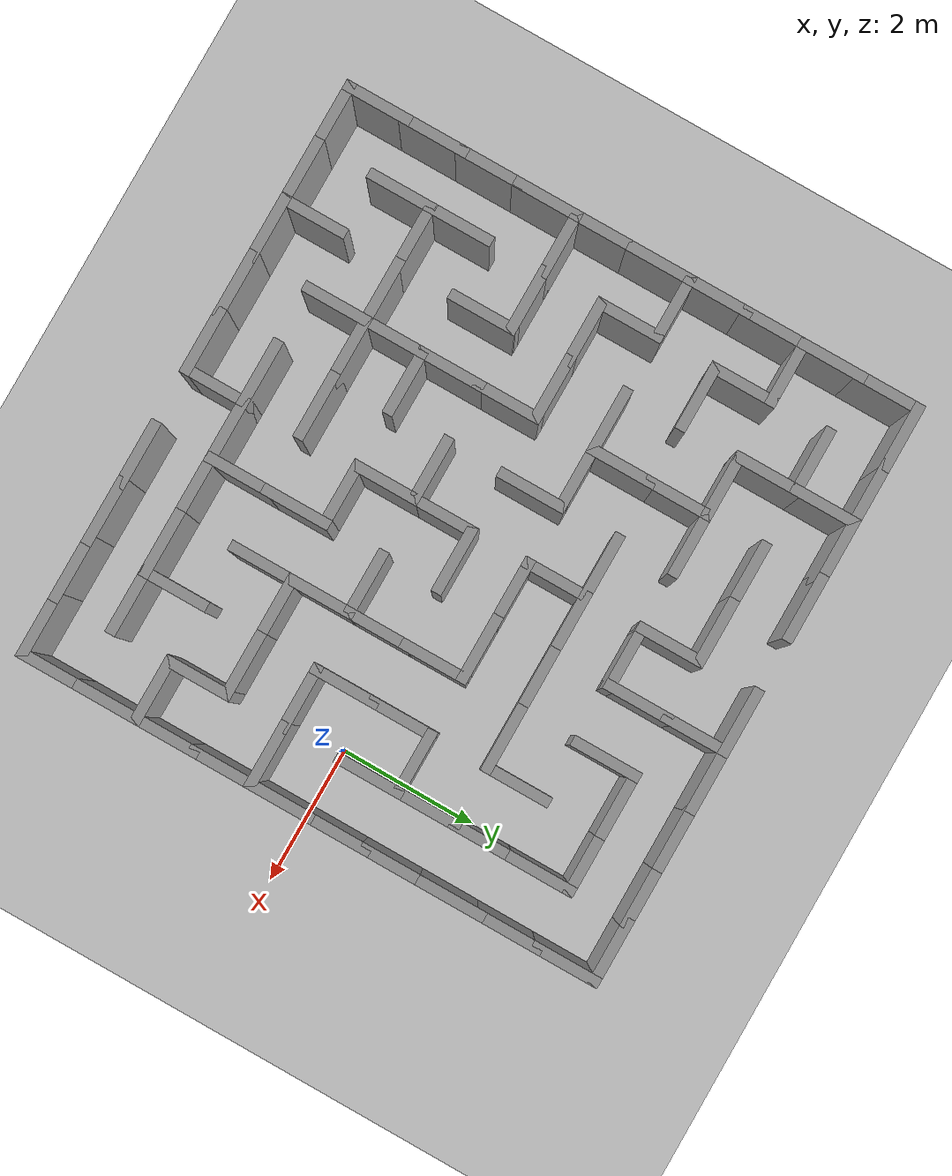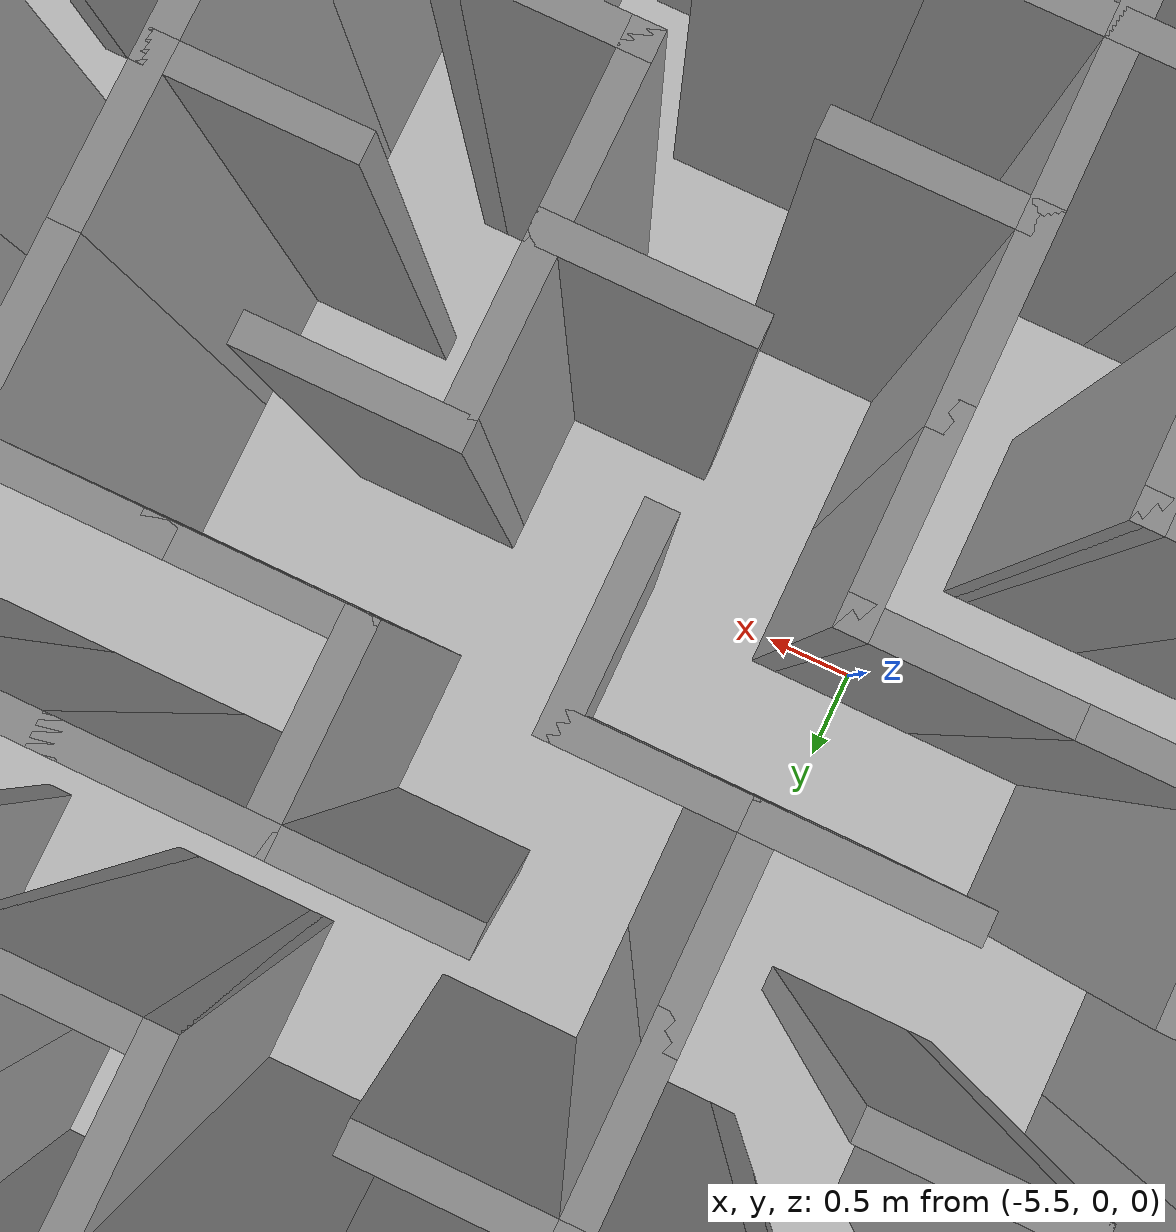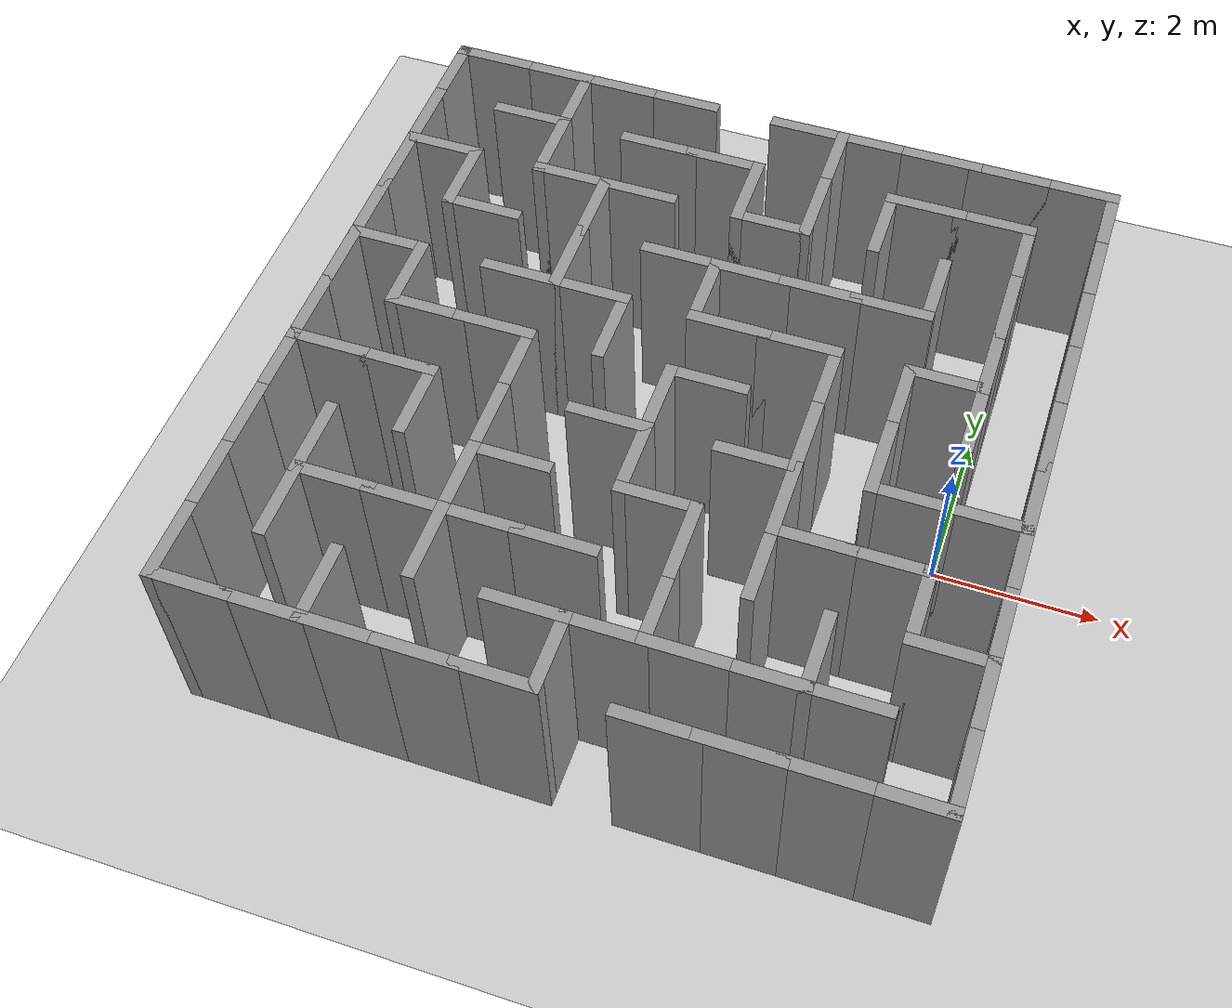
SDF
<?xml version="1.0"?>
<sdf version="1.6">
  <world name="default">

    <include>
      <uri>model://ground_plane</uri>
    </include>

    <include>
      <uri>model://sun</uri>
    </include>

    <scene>
      <shadows>false</shadows>
    </scene>

    <gui fullscreen='0'>
      <camera name='user_camera'>
        <pose frame=''>0.319654 -0.235002 15 0 1.5138 0.009599</pose>
        <view_controller>orbit</view_controller>
        <projection_type>perspective</projection_type>
      </camera>
    </gui>

    <physics type="ode">
      <real_time_update_rate>1000.0</real_time_update_rate>
      <max_step_size>0.001</max_step_size>
      <real_time_factor>1</real_time_factor>
      <ode>
        <solver>
          <type>quick</type>
          <iters>150</iters>
          <precon_iters>0</precon_iters>
          <sor>1.400000</sor>
          <use_dynamic_moi_rescaling>1</use_dynamic_moi_rescaling>
        </solver>
        <constraints>
          <cfm>0.00001</cfm>
          <erp>0.2</erp>
          <contact_max_correcting_vel>2000.000000</contact_max_correcting_vel>
          <contact_surface_layer>0.01000</contact_surface_layer>
        </constraints>
      </ode>
    </physics>

    <model name="maze_2">
      <static>1</static>
      <include>
        <uri>model://maze_2</uri>
      </include>
    </model>

  </world>
</sdf>

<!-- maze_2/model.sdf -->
<sdf version='1.6'>
  <model name='maze_2'>
    <pose frame=''>-3.32543 0.082709 0 0 -0 0</pose>
    <link name='Wall_0'>
      <collision name='Wall_0_Collision'>
        <geometry>
          <box>
            <size>1 0.15 2.5</size>
          </box>
        </geometry>
        <pose frame=''>0 0 1.25 0 -0 0</pose>
      </collision>
      <visual name='Wall_0_Visual'>
        <pose frame=''>0 0 1.25 0 -0 0</pose>
        <geometry>
          <box>
            <size>1 0.15 2.5</size>
          </box>
        </geometry>
        <material>
          <script>
            <uri>file://media/materials/scripts/gazebo.material</uri>
            <name>Gazebo/Grey</name>
          </script>
          <ambient>1 1 1 1</ambient>
        </material>
        <meta>
          <layer>0</layer>
        </meta>
      </visual>
      <pose frame=''>-3.825 4.25 0 0 -0 0</pose>
    </link>
    <link name='Wall_1'>
      <collision name='Wall_1_Collision'>
        <geometry>
          <box>
            <size>1 0.15 2.5</size>
          </box>
        </geometry>
        <pose frame=''>0 0 1.25 0 -0 0</pose>
      </collision>
      <visual name='Wall_1_Visual'>
        <pose frame=''>0 0 1.25 0 -0 0</pose>
        <geometry>
          <box>
            <size>1 0.15 2.5</size>
          </box>
        </geometry>
        <material>
          <script>
            <uri>file://media/materials/scripts/gazebo.material</uri>
            <name>Gazebo/Grey</name>
          </script>
          <ambient>1 1 1 1</ambient>
        </material>
        <meta>
          <layer>0</layer>
        </meta>
      </visual>
      <pose frame=''>-2.975 4.25 0 0 -0 0</pose>
    </link>
    <link name='Wall_10'>
      <collision name='Wall_10_Collision'>
        <geometry>
          <box>
            <size>1 0.15 2.5</size>
          </box>
        </geometry>
        <pose frame=''>0 0 1.25 0 -0 0</pose>
      </collision>
      <visual name='Wall_10_Visual'>
        <pose frame=''>0 0 1.25 0 -0 0</pose>
        <geometry>
          <box>
            <size>1 0.15 2.5</size>
          </box>
        </geometry>
        <material>
          <script>
            <uri>file://media/materials/scripts/gazebo.material</uri>
            <name>Gazebo/Grey</name>
          </script>
          <ambient>1 1 1 1</ambient>
        </material>
        <meta>
          <layer>0</layer>
        </meta>
      </visual>
      <pose frame=''>4.25 3.825 0 0 -0 -1.5708</pose>
    </link>
    <link name='Wall_100'>
      <collision name='Wall_100_Collision'>
        <geometry>
          <box>
            <size>1 0.15 2.5</size>
          </box>
        </geometry>
        <pose frame=''>0 0 1.25 0 -0 0</pose>
      </collision>
      <visual name='Wall_100_Visual'>
        <pose frame=''>0 0 1.25 0 -0 0</pose>
        <geometry>
          <box>
            <size>1 0.15 2.5</size>
          </box>
        </geometry>
        <material>
          <script>
            <uri>file://media/materials/scripts/gazebo.material</uri>
            <name>Gazebo/Grey</name>
          </script>
          <ambient>1 1 1 1</ambient>
        </material>
        <meta>
          <layer>0</layer>
        </meta>
      </visual>
      <pose frame=''>-3.825 -0.85 0 0 -0 0</pose>
    </link>
    <link name='Wall_101'>
      <collision name='Wall_101_Collision'>
        <geometry>
          <box>
            <size>1 0.15 2.5</size>
          </box>
        </geometry>
        <pose frame=''>0 0 1.25 0 -0 0</pose>
      </collision>
      <visual name='Wall_101_Visual'>
        <pose frame=''>0 0 1.25 0 -0 0</pose>
        <geometry>
          <box>
            <size>1 0.15 2.5</size>
          </box>
        </geometry>
        <material>
          <script>
            <uri>file://media/materials/scripts/gazebo.material</uri>
            <name>Gazebo/Grey</name>
          </script>
          <ambient>1 1 1 1</ambient>
        </material>
        <meta>
          <layer>0</layer>
        </meta>
      </visual>
      <pose frame=''>-2.975 -0.85 0 0 -0 0</pose>
    </link>
    <link name='Wall_104'>
      <collision name='Wall_104_Collision'>
        <geometry>
          <box>
            <size>1 0.15 2.5</size>
          </box>
        </geometry>
        <pose frame=''>0 0 1.25 0 -0 0</pose>
      </collision>
      <visual name='Wall_104_Visual'>
        <pose frame=''>0 0 1.25 0 -0 0</pose>
        <geometry>
          <box>
            <size>1 0.15 2.5</size>
          </box>
        </geometry>
        <material>
          <script>
            <uri>file://media/materials/scripts/gazebo.material</uri>
            <name>Gazebo/Grey</name>
          </script>
          <ambient>1 1 1 1</ambient>
        </material>
        <meta>
          <layer>0</layer>
        </meta>
      </visual>
      <pose frame=''>-0.425 -0.85 0 0 -0 0</pose>
    </link>
    <link name='Wall_106'>
      <collision name='Wall_106_Collision'>
        <geometry>
          <box>
            <size>1 0.15 2.5</size>
          </box>
        </geometry>
        <pose frame=''>0 0 1.25 0 -0 0</pose>
      </collision>
      <visual name='Wall_106_Visual'>
        <pose frame=''>0 0 1.25 0 -0 0</pose>
        <geometry>
          <box>
            <size>1 0.15 2.5</size>
          </box>
        </geometry>
        <material>
          <script>
            <uri>file://media/materials/scripts/gazebo.material</uri>
            <name>Gazebo/Grey</name>
          </script>
          <ambient>1 1 1 1</ambient>
        </material>
        <meta>
          <layer>0</layer>
        </meta>
      </visual>
      <pose frame=''>1.275 -0.85 0 0 -0 0</pose>
    </link>
    <link name='Wall_108'>
      <collision name='Wall_108_Collision'>
        <geometry>
          <box>
            <size>1 0.15 2.5</size>
          </box>
        </geometry>
        <pose frame=''>0 0 1.25 0 -0 0</pose>
      </collision>
      <visual name='Wall_108_Visual'>
        <pose frame=''>0 0 1.25 0 -0 0</pose>
        <geometry>
          <box>
            <size>1 0.15 2.5</size>
          </box>
        </geometry>
        <material>
          <script>
            <uri>file://media/materials/scripts/gazebo.material</uri>
            <name>Gazebo/Grey</name>
          </script>
          <ambient>1 1 1 1</ambient>
        </material>
        <meta>
          <layer>0</layer>
        </meta>
      </visual>
      <pose frame=''>2.975 -0.85 0 0 -0 0</pose>
    </link>
    <link name='Wall_109'>
      <collision name='Wall_109_Collision'>
        <geometry>
          <box>
            <size>1 0.15 2.5</size>
          </box>
        </geometry>
        <pose frame=''>0 0 1.25 0 -0 0</pose>
      </collision>
      <visual name='Wall_109_Visual'>
        <pose frame=''>0 0 1.25 0 -0 0</pose>
        <geometry>
          <box>
            <size>1 0.15 2.5</size>
          </box>
        </geometry>
        <material>
          <script>
            <uri>file://media/materials/scripts/gazebo.material</uri>
            <name>Gazebo/Grey</name>
          </script>
          <ambient>1 1 1 1</ambient>
        </material>
        <meta>
          <layer>0</layer>
        </meta>
      </visual>
      <pose frame=''>3.825 -0.85 0 0 -0 0</pose>
    </link>
    <link name='Wall_11'>
      <collision name='Wall_11_Collision'>
        <geometry>
          <box>
            <size>1 0.15 2.5</size>
          </box>
        </geometry>
        <pose frame=''>0 0 1.25 0 -0 0</pose>
      </collision>
      <visual name='Wall_11_Visual'>
        <pose frame=''>0 0 1.25 0 -0 0</pose>
        <geometry>
          <box>
            <size>1 0.15 2.5</size>
          </box>
        </geometry>
        <material>
          <script>
            <uri>file://media/materials/scripts/gazebo.material</uri>
            <name>Gazebo/Grey</name>
          </script>
          <ambient>1 1 1 1</ambient>
        </material>
        <meta>
          <layer>0</layer>
        </meta>
      </visual>
      <pose frame=''>4.25 2.975 0 0 -0 -1.5708</pose>
    </link>
    <link name='Wall_112'>
      <collision name='Wall_112_Collision'>
        <geometry>
          <box>
            <size>1 0.15 2.5</size>
          </box>
        </geometry>
        <pose frame=''>0 0 1.25 0 -0 0</pose>
      </collision>
      <visual name='Wall_112_Visual'>
        <pose frame=''>0 0 1.25 0 -0 0</pose>
        <geometry>
          <box>
            <size>1 0.15 2.5</size>
          </box>
        </geometry>
        <material>
          <script>
            <uri>file://media/materials/scripts/gazebo.material</uri>
            <name>Gazebo/Grey</name>
          </script>
          <ambient>1 1 1 1</ambient>
        </material>
        <meta>
          <layer>0</layer>
        </meta>
      </visual>
      <pose frame=''>2.975 -1.7 0 0 -0 3.14159</pose>
    </link>
    <link name='Wall_113'>
      <collision name='Wall_113_Collision'>
        <geometry>
          <box>
            <size>1 0.15 2.5</size>
          </box>
        </geometry>
        <pose frame=''>0 0 1.25 0 -0 0</pose>
      </collision>
      <visual name='Wall_113_Visual'>
        <pose frame=''>0 0 1.25 0 -0 0</pose>
        <geometry>
          <box>
            <size>1 0.15 2.5</size>
          </box>
        </geometry>
        <material>
          <script>
            <uri>file://media/materials/scripts/gazebo.material</uri>
            <name>Gazebo/Grey</name>
          </script>
          <ambient>1 1 1 1</ambient>
        </material>
        <meta>
          <layer>0</layer>
        </meta>
      </visual>
      <pose frame=''>2.125 -1.7 0 0 -0 3.14159</pose>
    </link>
    <link name='Wall_115'>
      <collision name='Wall_115_Collision'>
        <geometry>
          <box>
            <size>1 0.15 2.5</size>
          </box>
        </geometry>
        <pose frame=''>0 0 1.25 0 -0 0</pose>
      </collision>
      <visual name='Wall_115_Visual'>
        <pose frame=''>0 0 1.25 0 -0 0</pose>
        <geometry>
          <box>
            <size>1 0.15 2.5</size>
          </box>
        </geometry>
        <material>
          <script>
            <uri>file://media/materials/scripts/gazebo.material</uri>
            <name>Gazebo/Grey</name>
          </script>
          <ambient>1 1 1 1</ambient>
        </material>
        <meta>
          <layer>0</layer>
        </meta>
      </visual>
      <pose frame=''>0.425 -1.7 0 0 -0 3.14159</pose>
    </link>
    <link name='Wall_117'>
      <collision name='Wall_117_Collision'>
        <geometry>
          <box>
            <size>1 0.15 2.5</size>
          </box>
        </geometry>
        <pose frame=''>0 0 1.25 0 -0 0</pose>
      </collision>
      <visual name='Wall_117_Visual'>
        <pose frame=''>0 0 1.25 0 -0 0</pose>
        <geometry>
          <box>
            <size>1 0.15 2.5</size>
          </box>
        </geometry>
        <material>
          <script>
            <uri>file://media/materials/scripts/gazebo.material</uri>
            <name>Gazebo/Grey</name>
          </script>
          <ambient>1 1 1 1</ambient>
        </material>
        <meta>
          <layer>0</layer>
        </meta>
      </visual>
      <pose frame=''>-1.275 -1.7 0 0 -0 3.14159</pose>
    </link>
    <link name='Wall_12'>
      <collision name='Wall_12_Collision'>
        <geometry>
          <box>
            <size>1 0.15 2.5</size>
          </box>
        </geometry>
        <pose frame=''>0 0 1.25 0 -0 0</pose>
      </collision>
      <visual name='Wall_12_Visual'>
        <pose frame=''>0 0 1.25 0 -0 0</pose>
        <geometry>
          <box>
            <size>1 0.15 2.5</size>
          </box>
        </geometry>
        <material>
          <script>
            <uri>file://media/materials/scripts/gazebo.material</uri>
            <name>Gazebo/Grey</name>
          </script>
          <ambient>1 1 1 1</ambient>
        </material>
        <meta>
          <layer>0</layer>
        </meta>
      </visual>
      <pose frame=''>4.25 2.125 0 0 -0 -1.5708</pose>
    </link>
    <link name='Wall_124'>
      <collision name='Wall_124_Collision'>
        <geometry>
          <box>
            <size>1 0.15 2.5</size>
          </box>
        </geometry>
        <pose frame=''>0 0 1.25 0 -0 0</pose>
      </collision>
      <visual name='Wall_124_Visual'>
        <pose frame=''>0 0 1.25 0 -0 0</pose>
        <geometry>
          <box>
            <size>1 0.15 2.5</size>
          </box>
        </geometry>
        <material>
          <script>
            <uri>file://media/materials/scripts/gazebo.material</uri>
            <name>Gazebo/Grey</name>
          </script>
          <ambient>1 1 1 1</ambient>
        </material>
        <meta>
          <layer>0</layer>
        </meta>
      </visual>
      <pose frame=''>-2.975 -2.55 0 0 -0 0</pose>
    </link>
    <link name='Wall_125'>
      <collision name='Wall_125_Collision'>
        <geometry>
          <box>
            <size>1 0.15 2.5</size>
          </box>
        </geometry>
        <pose frame=''>0 0 1.25 0 -0 0</pose>
      </collision>
      <visual name='Wall_125_Visual'>
        <pose frame=''>0 0 1.25 0 -0 0</pose>
        <geometry>
          <box>
            <size>1 0.15 2.5</size>
          </box>
        </geometry>
        <material>
          <script>
            <uri>file://media/materials/scripts/gazebo.material</uri>
            <name>Gazebo/Grey</name>
          </script>
          <ambient>1 1 1 1</ambient>
        </material>
        <meta>
          <layer>0</layer>
        </meta>
      </visual>
      <pose frame=''>-2.125 -2.55 0 0 -0 0</pose>
    </link>
    <link name='Wall_126'>
      <collision name='Wall_126_Collision'>
        <geometry>
          <box>
            <size>1 0.15 2.5</size>
          </box>
        </geometry>
        <pose frame=''>0 0 1.25 0 -0 0</pose>
      </collision>
      <visual name='Wall_126_Visual'>
        <pose frame=''>0 0 1.25 0 -0 0</pose>
        <geometry>
          <box>
            <size>1 0.15 2.5</size>
          </box>
        </geometry>
        <material>
          <script>
            <uri>file://media/materials/scripts/gazebo.material</uri>
            <name>Gazebo/Grey</name>
          </script>
          <ambient>1 1 1 1</ambient>
        </material>
        <meta>
          <layer>0</layer>
        </meta>
      </visual>
      <pose frame=''>-1.275 -2.55 0 0 -0 0</pose>
    </link>
    <link name='Wall_127'>
      <collision name='Wall_127_Collision'>
        <geometry>
          <box>
            <size>1 0.15 2.5</size>
          </box>
        </geometry>
        <pose frame=''>0 0 1.25 0 -0 0</pose>
      </collision>
      <visual name='Wall_127_Visual'>
        <pose frame=''>0 0 1.25 0 -0 0</pose>
        <geometry>
          <box>
            <size>1 0.15 2.5</size>
          </box>
        </geometry>
        <material>
          <script>
            <uri>file://media/materials/scripts/gazebo.material</uri>
            <name>Gazebo/Grey</name>
          </script>
          <ambient>1 1 1 1</ambient>
        </material>
        <meta>
          <layer>0</layer>
        </meta>
      </visual>
      <pose frame=''>-0.425 -2.55 0 0 -0 0</pose>
    </link>
    <link name='Wall_13'>
      <collision name='Wall_13_Collision'>
        <geometry>
          <box>
            <size>1 0.15 2.5</size>
          </box>
        </geometry>
        <pose frame=''>0 0 1.25 0 -0 0</pose>
      </collision>
      <visual name='Wall_13_Visual'>
        <pose frame=''>0 0 1.25 0 -0 0</pose>
        <geometry>
          <box>
            <size>1 0.15 2.5</size>
          </box>
        </geometry>
        <material>
          <script>
            <uri>file://media/materials/scripts/gazebo.material</uri>
            <name>Gazebo/Grey</name>
          </script>
          <ambient>1 1 1 1</ambient>
        </material>
        <meta>
          <layer>0</layer>
        </meta>
      </visual>
      <pose frame=''>4.25 1.275 0 0 -0 -1.5708</pose>
    </link>
    <link name='Wall_132'>
      <collision name='Wall_132_Collision'>
        <geometry>
          <box>
            <size>1 0.15 2.5</size>
          </box>
        </geometry>
        <pose frame=''>0 0 1.25 0 -0 0</pose>
      </collision>
      <visual name='Wall_132_Visual'>
        <pose frame=''>0 0 1.25 0 -0 0</pose>
        <geometry>
          <box>
            <size>1 0.15 2.5</size>
          </box>
        </geometry>
        <material>
          <script>
            <uri>file://media/materials/scripts/gazebo.material</uri>
            <name>Gazebo/Grey</name>
          </script>
          <ambient>1 1 1 1</ambient>
        </material>
        <meta>
          <layer>0</layer>
        </meta>
      </visual>
      <pose frame=''>3.825 -2.55 0 0 -0 0</pose>
    </link>
    <link name='Wall_138'>
      <collision name='Wall_138_Collision'>
        <geometry>
          <box>
            <size>1 0.15 2.5</size>
          </box>
        </geometry>
        <pose frame=''>0 0 1.25 0 -0 0</pose>
      </collision>
      <visual name='Wall_138_Visual'>
        <pose frame=''>0 0 1.25 0 -0 0</pose>
        <geometry>
          <box>
            <size>1 0.15 2.5</size>
          </box>
        </geometry>
        <material>
          <script>
            <uri>file://media/materials/scripts/gazebo.material</uri>
            <name>Gazebo/Grey</name>
          </script>
          <ambient>1 1 1 1</ambient>
        </material>
        <meta>
          <layer>0</layer>
        </meta>
      </visual>
      <pose frame=''>-0.425 -3.4 0 0 -0 0</pose>
    </link>
    <link name='Wall_139'>
      <collision name='Wall_139_Collision'>
        <geometry>
          <box>
            <size>1 0.15 2.5</size>
          </box>
        </geometry>
        <pose frame=''>0 0 1.25 0 -0 0</pose>
      </collision>
      <visual name='Wall_139_Visual'>
        <pose frame=''>0 0 1.25 0 -0 0</pose>
        <geometry>
          <box>
            <size>1 0.15 2.5</size>
          </box>
        </geometry>
        <material>
          <script>
            <uri>file://media/materials/scripts/gazebo.material</uri>
            <name>Gazebo/Grey</name>
          </script>
          <ambient>1 1 1 1</ambient>
        </material>
        <meta>
          <layer>0</layer>
        </meta>
      </visual>
      <pose frame=''>0.425 -3.4 0 0 -0 0</pose>
    </link>
    <link name='Wall_14'>
      <collision name='Wall_14_Collision'>
        <geometry>
          <box>
            <size>1 0.15 2.5</size>
          </box>
        </geometry>
        <pose frame=''>0 0 1.25 0 -0 0</pose>
      </collision>
      <visual name='Wall_14_Visual'>
        <pose frame=''>0 0 1.25 0 -0 0</pose>
        <geometry>
          <box>
            <size>1 0.15 2.5</size>
          </box>
        </geometry>
        <material>
          <script>
            <uri>file://media/materials/scripts/gazebo.material</uri>
            <name>Gazebo/Grey</name>
          </script>
          <ambient>1 1 1 1</ambient>
        </material>
        <meta>
          <layer>0</layer>
        </meta>
      </visual>
      <pose frame=''>4.25 0.425 0 0 -0 -1.5708</pose>
    </link>
    <link name='Wall_140'>
      <collision name='Wall_140_Collision'>
        <geometry>
          <box>
            <size>1 0.15 2.5</size>
          </box>
        </geometry>
        <pose frame=''>0 0 1.25 0 -0 0</pose>
      </collision>
      <visual name='Wall_140_Visual'>
        <pose frame=''>0 0 1.25 0 -0 0</pose>
        <geometry>
          <box>
            <size>1 0.15 2.5</size>
          </box>
        </geometry>
        <material>
          <script>
            <uri>file://media/materials/scripts/gazebo.material</uri>
            <name>Gazebo/Grey</name>
          </script>
          <ambient>1 1 1 1</ambient>
        </material>
        <meta>
          <layer>0</layer>
        </meta>
      </visual>
      <pose frame=''>1.275 -3.4 0 0 -0 0</pose>
    </link>
    <link name='Wall_141'>
      <collision name='Wall_141_Collision'>
        <geometry>
          <box>
            <size>1 0.15 2.5</size>
          </box>
        </geometry>
        <pose frame=''>0 0 1.25 0 -0 0</pose>
      </collision>
      <visual name='Wall_141_Visual'>
        <pose frame=''>0 0 1.25 0 -0 0</pose>
        <geometry>
          <box>
            <size>1 0.15 2.5</size>
          </box>
        </geometry>
        <material>
          <script>
            <uri>file://media/materials/scripts/gazebo.material</uri>
            <name>Gazebo/Grey</name>
          </script>
          <ambient>1 1 1 1</ambient>
        </material>
        <meta>
          <layer>0</layer>
        </meta>
      </visual>
      <pose frame=''>2.125 -3.4 0 0 -0 0</pose>
    </link>
    <link name='Wall_142'>
      <collision name='Wall_142_Collision'>
        <geometry>
          <box>
            <size>1 0.15 2.5</size>
          </box>
        </geometry>
        <pose frame=''>0 0 1.25 0 -0 0</pose>
      </collision>
      <visual name='Wall_142_Visual'>
        <pose frame=''>0 0 1.25 0 -0 0</pose>
        <geometry>
          <box>
            <size>1 0.15 2.5</size>
          </box>
        </geometry>
        <material>
          <script>
            <uri>file://media/materials/scripts/gazebo.material</uri>
            <name>Gazebo/Grey</name>
          </script>
          <ambient>1 1 1 1</ambient>
        </material>
        <meta>
          <layer>0</layer>
        </meta>
      </visual>
      <pose frame=''>2.975 -3.4 0 0 -0 0</pose>
    </link>
    <link name='Wall_147'>
      <collision name='Wall_147_Collision'>
        <geometry>
          <box>
            <size>1 0.15 2.5</size>
          </box>
        </geometry>
        <pose frame=''>0 0 1.25 0 -0 0</pose>
      </collision>
      <visual name='Wall_147_Visual'>
        <pose frame=''>0 0 1.25 0 -0 0</pose>
        <geometry>
          <box>
            <size>1 0.15 2.5</size>
          </box>
        </geometry>
        <material>
          <script>
            <uri>file://media/materials/scripts/gazebo.material</uri>
            <name>Gazebo/Grey</name>
          </script>
          <ambient>1 1 1 1</ambient>
        </material>
        <meta>
          <layer>0</layer>
        </meta>
      </visual>
      <pose frame=''>-3.4 2.125 0 0 -0 -1.5708</pose>
    </link>
    <link name='Wall_149'>
      <collision name='Wall_149_Collision'>
        <geometry>
          <box>
            <size>1 0.15 2.5</size>
          </box>
        </geometry>
        <pose frame=''>0 0 1.25 0 -0 0</pose>
      </collision>
      <visual name='Wall_149_Visual'>
        <pose frame=''>0 0 1.25 0 -0 0</pose>
        <geometry>
          <box>
            <size>1 0.15 2.5</size>
          </box>
        </geometry>
        <material>
          <script>
            <uri>file://media/materials/scripts/gazebo.material</uri>
            <name>Gazebo/Grey</name>
          </script>
          <ambient>1 1 1 1</ambient>
        </material>
        <meta>
          <layer>0</layer>
        </meta>
      </visual>
      <pose frame=''>-3.4 0.425 0 0 -0 -1.5708</pose>
    </link>
    <link name='Wall_15'>
      <collision name='Wall_15_Collision'>
        <geometry>
          <box>
            <size>1 0.15 2.5</size>
          </box>
        </geometry>
        <pose frame=''>0 0 1.25 0 -0 0</pose>
      </collision>
      <visual name='Wall_15_Visual'>
        <pose frame=''>0 0 1.25 0 -0 0</pose>
        <geometry>
          <box>
            <size>1 0.15 2.5</size>
          </box>
        </geometry>
        <material>
          <script>
            <uri>file://media/materials/scripts/gazebo.material</uri>
            <name>Gazebo/Grey</name>
          </script>
          <ambient>1 1 1 1</ambient>
        </material>
        <meta>
          <layer>0</layer>
        </meta>
      </visual>
      <pose frame=''>4.25 -0.425 0 0 -0 -1.5708</pose>
    </link>
    <link name='Wall_152'>
      <collision name='Wall_152_Collision'>
        <geometry>
          <box>
            <size>1 0.15 2.5</size>
          </box>
        </geometry>
        <pose frame=''>0 0 1.25 0 -0 0</pose>
      </collision>
      <visual name='Wall_152_Visual'>
        <pose frame=''>0 0 1.25 0 -0 0</pose>
        <geometry>
          <box>
            <size>1 0.15 2.5</size>
          </box>
        </geometry>
        <material>
          <script>
            <uri>file://media/materials/scripts/gazebo.material</uri>
            <name>Gazebo/Grey</name>
          </script>
          <ambient>1 1 1 1</ambient>
        </material>
        <meta>
          <layer>0</layer>
        </meta>
      </visual>
      <pose frame=''>-3.4 -2.125 0 0 -0 -1.5708</pose>
    </link>
    <link name='Wall_153'>
      <collision name='Wall_153_Collision'>
        <geometry>
          <box>
            <size>1 0.15 2.5</size>
          </box>
        </geometry>
        <pose frame=''>0 0 1.25 0 -0 0</pose>
      </collision>
      <visual name='Wall_153_Visual'>
        <pose frame=''>0 0 1.25 0 -0 0</pose>
        <geometry>
          <box>
            <size>1 0.15 2.5</size>
          </box>
        </geometry>
        <material>
          <script>
            <uri>file://media/materials/scripts/gazebo.material</uri>
            <name>Gazebo/Grey</name>
          </script>
          <ambient>1 1 1 1</ambient>
        </material>
        <meta>
          <layer>0</layer>
        </meta>
      </visual>
      <pose frame=''>-3.4 -2.975 0 0 -0 -1.5708</pose>
    </link>
    <link name='Wall_156'>
      <collision name='Wall_156_Collision'>
        <geometry>
          <box>
            <size>1 0.15 2.5</size>
          </box>
        </geometry>
        <pose frame=''>0 0 1.25 0 -0 0</pose>
      </collision>
      <visual name='Wall_156_Visual'>
        <pose frame=''>0 0 1.25 0 -0 0</pose>
        <geometry>
          <box>
            <size>1 0.15 2.5</size>
          </box>
        </geometry>
        <material>
          <script>
            <uri>file://media/materials/scripts/gazebo.material</uri>
            <name>Gazebo/Grey</name>
          </script>
          <ambient>1 1 1 1</ambient>
        </material>
        <meta>
          <layer>0</layer>
        </meta>
      </visual>
      <pose frame=''>-2.55 3.825 0 0 -0 -1.5708</pose>
    </link>
    <link name='Wall_157'>
      <collision name='Wall_157_Collision'>
        <geometry>
          <box>
            <size>1 0.15 2.5</size>
          </box>
        </geometry>
        <pose frame=''>0 0 1.25 0 -0 0</pose>
      </collision>
      <visual name='Wall_157_Visual'>
        <pose frame=''>0 0 1.25 0 -0 0</pose>
        <geometry>
          <box>
            <size>1 0.15 2.5</size>
          </box>
        </geometry>
        <material>
          <script>
            <uri>file://media/materials/scripts/gazebo.material</uri>
            <name>Gazebo/Grey</name>
          </script>
          <ambient>1 1 1 1</ambient>
        </material>
        <meta>
          <layer>0</layer>
        </meta>
      </visual>
      <pose frame=''>-2.55 2.975 0 0 -0 -1.5708</pose>
    </link>
    <link name='Wall_162'>
      <collision name='Wall_162_Collision'>
        <geometry>
          <box>
            <size>1 0.15 2.5</size>
          </box>
        </geometry>
        <pose frame=''>0 0 1.25 0 -0 0</pose>
      </collision>
      <visual name='Wall_162_Visual'>
        <pose frame=''>0 0 1.25 0 -0 0</pose>
        <geometry>
          <box>
            <size>1 0.15 2.5</size>
          </box>
        </geometry>
        <material>
          <script>
            <uri>file://media/materials/scripts/gazebo.material</uri>
            <name>Gazebo/Grey</name>
          </script>
          <ambient>1 1 1 1</ambient>
        </material>
        <meta>
          <layer>0</layer>
        </meta>
      </visual>
      <pose frame=''>-2.55 -1.275 0 0 -0 -1.5708</pose>
    </link>
    <link name='Wall_165'>
      <collision name='Wall_165_Collision'>
        <geometry>
          <box>
            <size>1 0.15 2.5</size>
          </box>
        </geometry>
        <pose frame=''>0 0 1.25 0 -0 0</pose>
      </collision>
      <visual name='Wall_165_Visual'>
        <pose frame=''>0 0 1.25 0 -0 0</pose>
        <geometry>
          <box>
            <size>1 0.15 2.5</size>
          </box>
        </geometry>
        <material>
          <script>
            <uri>file://media/materials/scripts/gazebo.material</uri>
            <name>Gazebo/Grey</name>
          </script>
          <ambient>1 1 1 1</ambient>
        </material>
        <meta>
          <layer>0</layer>
        </meta>
      </visual>
      <pose frame=''>-2.55 -3.825 0 0 -0 -1.5708</pose>
    </link>
    <link name='Wall_169'>
      <collision name='Wall_169_Collision'>
        <geometry>
          <box>
            <size>1 0.15 2.5</size>
          </box>
        </geometry>
        <pose frame=''>0 0 1.25 0 -0 0</pose>
      </collision>
      <visual name='Wall_169_Visual'>
        <pose frame=''>0 0 1.25 0 -0 0</pose>
        <geometry>
          <box>
            <size>1 0.15 2.5</size>
          </box>
        </geometry>
        <material>
          <script>
            <uri>file://media/materials/scripts/gazebo.material</uri>
            <name>Gazebo/Grey</name>
          </script>
          <ambient>1 1 1 1</ambient>
        </material>
        <meta>
          <layer>0</layer>
        </meta>
      </visual>
      <pose frame=''>-1.7 2.125 0 0 -0 -1.5708</pose>
    </link>
    <link name='Wall_170'>
      <collision name='Wall_170_Collision'>
        <geometry>
          <box>
            <size>1 0.15 2.5</size>
          </box>
        </geometry>
        <pose frame=''>0 0 1.25 0 -0 0</pose>
      </collision>
      <visual name='Wall_170_Visual'>
        <pose frame=''>0 0 1.25 0 -0 0</pose>
        <geometry>
          <box>
            <size>1 0.15 2.5</size>
          </box>
        </geometry>
        <material>
          <script>
            <uri>file://media/materials/scripts/gazebo.material</uri>
            <name>Gazebo/Grey</name>
          </script>
          <ambient>1 1 1 1</ambient>
        </material>
        <meta>
          <layer>0</layer>
        </meta>
      </visual>
      <pose frame=''>-1.7 1.275 0 0 -0 -1.5708</pose>
    </link>
    <link name='Wall_172'>
      <collision name='Wall_172_Collision'>
        <geometry>
          <box>
            <size>1 0.15 2.5</size>
          </box>
        </geometry>
        <pose frame=''>0 0 1.25 0 -0 0</pose>
      </collision>
      <visual name='Wall_172_Visual'>
        <pose frame=''>0 0 1.25 0 -0 0</pose>
        <geometry>
          <box>
            <size>1 0.15 2.5</size>
          </box>
        </geometry>
        <material>
          <script>
            <uri>file://media/materials/scripts/gazebo.material</uri>
            <name>Gazebo/Grey</name>
          </script>
          <ambient>1 1 1 1</ambient>
        </material>
        <meta>
          <layer>0</layer>
        </meta>
      </visual>
      <pose frame=''>-1.7 -0.425 0 0 -0 -1.5708</pose>
    </link>
    <link name='Wall_173'>
      <collision name='Wall_173_Collision'>
        <geometry>
          <box>
            <size>1 0.15 2.5</size>
          </box>
        </geometry>
        <pose frame=''>0 0 1.25 0 -0 0</pose>
      </collision>
      <visual name='Wall_173_Visual'>
        <pose frame=''>0 0 1.25 0 -0 0</pose>
        <geometry>
          <box>
            <size>1 0.15 2.5</size>
          </box>
        </geometry>
        <material>
          <script>
            <uri>file://media/materials/scripts/gazebo.material</uri>
            <name>Gazebo/Grey</name>
          </script>
          <ambient>1 1 1 1</ambient>
        </material>
        <meta>
          <layer>0</layer>
        </meta>
      </visual>
      <pose frame=''>-1.7 -1.275 0 0 -0 -1.5708</pose>
    </link>
    <link name='Wall_174'>
      <collision name='Wall_174_Collision'>
        <geometry>
          <box>
            <size>1 0.15 2.5</size>
          </box>
        </geometry>
        <pose frame=''>0 0 1.25 0 -0 0</pose>
      </collision>
      <visual name='Wall_174_Visual'>
        <pose frame=''>0 0 1.25 0 -0 0</pose>
        <geometry>
          <box>
            <size>1 0.15 2.5</size>
          </box>
        </geometry>
        <material>
          <script>
            <uri>file://media/materials/scripts/gazebo.material</uri>
            <name>Gazebo/Grey</name>
          </script>
          <ambient>1 1 1 1</ambient>
        </material>
        <meta>
          <layer>0</layer>
        </meta>
      </visual>
      <pose frame=''>-1.7 -2.125 0 0 -0 -1.5708</pose>
    </link>
    <link name='Wall_175'>
      <collision name='Wall_175_Collision'>
        <geometry>
          <box>
            <size>1 0.15 2.5</size>
          </box>
        </geometry>
        <pose frame=''>0 0 1.25 0 -0 0</pose>
      </collision>
      <visual name='Wall_175_Visual'>
        <pose frame=''>0 0 1.25 0 -0 0</pose>
        <geometry>
          <box>
            <size>1 0.15 2.5</size>
          </box>
        </geometry>
        <material>
          <script>
            <uri>file://media/materials/scripts/gazebo.material</uri>
            <name>Gazebo/Grey</name>
          </script>
          <ambient>1 1 1 1</ambient>
        </material>
        <meta>
          <layer>0</layer>
        </meta>
      </visual>
      <pose frame=''>-1.7 -2.975 0 0 -0 -1.5708</pose>
    </link>
    <link name='Wall_18'>
      <collision name='Wall_18_Collision'>
        <geometry>
          <box>
            <size>1 0.15 2.5</size>
          </box>
        </geometry>
        <pose frame=''>0 0 1.25 0 -0 0</pose>
      </collision>
      <visual name='Wall_18_Visual'>
        <pose frame=''>0 0 1.25 0 -0 0</pose>
        <geometry>
          <box>
            <size>1 0.15 2.5</size>
          </box>
        </geometry>
        <material>
          <script>
            <uri>file://media/materials/scripts/gazebo.material</uri>
            <name>Gazebo/Grey</name>
          </script>
          <ambient>1 1 1 1</ambient>
        </material>
        <meta>
          <layer>0</layer>
        </meta>
      </visual>
      <pose frame=''>4.25 -1.275 0 0 -0 -1.5708</pose>
    </link>
    <link name='Wall_182'>
      <collision name='Wall_182_Collision'>
        <geometry>
          <box>
            <size>1 0.15 2.5</size>
          </box>
        </geometry>
        <pose frame=''>0 0 1.25 0 -0 0</pose>
      </collision>
      <visual name='Wall_182_Visual'>
        <pose frame=''>0 0 1.25 0 -0 0</pose>
        <geometry>
          <box>
            <size>1 0.15 2.5</size>
          </box>
        </geometry>
        <material>
          <script>
            <uri>file://media/materials/scripts/gazebo.material</uri>
            <name>Gazebo/Grey</name>
          </script>
          <ambient>1 1 1 1</ambient>
        </material>
        <meta>
          <layer>0</layer>
        </meta>
      </visual>
      <pose frame=''>-0.85 0.425 0 0 -0 -1.5708</pose>
    </link>
    <link name='Wall_19'>
      <collision name='Wall_19_Collision'>
        <geometry>
          <box>
            <size>1 0.15 2.5</size>
          </box>
        </geometry>
        <pose frame=''>0 0 1.25 0 -0 0</pose>
      </collision>
      <visual name='Wall_19_Visual'>
        <pose frame=''>0 0 1.25 0 -0 0</pose>
        <geometry>
          <box>
            <size>1 0.15 2.5</size>
          </box>
        </geometry>
        <material>
          <script>
            <uri>file://media/materials/scripts/gazebo.material</uri>
            <name>Gazebo/Grey</name>
          </script>
          <ambient>1 1 1 1</ambient>
        </material>
        <meta>
          <layer>0</layer>
        </meta>
      </visual>
      <pose frame=''>4.25 -2.125 0 0 -0 -1.5708</pose>
    </link>
    <link name='Wall_190'>
      <collision name='Wall_190_Collision'>
        <geometry>
          <box>
            <size>1 0.15 2.5</size>
          </box>
        </geometry>
        <pose frame=''>0 0 1.25 0 -0 0</pose>
      </collision>
      <visual name='Wall_190_Visual'>
        <pose frame=''>0 0 1.25 0 -0 0</pose>
        <geometry>
          <box>
            <size>1 0.15 2.5</size>
          </box>
        </geometry>
        <material>
          <script>
            <uri>file://media/materials/scripts/gazebo.material</uri>
            <name>Gazebo/Grey</name>
          </script>
          <ambient>1 1 1 1</ambient>
        </material>
        <meta>
          <layer>0</layer>
        </meta>
      </visual>
      <pose frame=''>0 2.975 0 0 -0 -1.5708</pose>
    </link>
    <link name='Wall_192'>
      <collision name='Wall_192_Collision'>
        <geometry>
          <box>
            <size>1 0.15 2.5</size>
          </box>
        </geometry>
        <pose frame=''>0 0 1.25 0 -0 0</pose>
      </collision>
      <visual name='Wall_192_Visual'>
        <pose frame=''>0 0 1.25 0 -0 0</pose>
        <geometry>
          <box>
            <size>1 0.15 2.5</size>
          </box>
        </geometry>
        <material>
          <script>
            <uri>file://media/materials/scripts/gazebo.material</uri>
            <name>Gazebo/Grey</name>
          </script>
          <ambient>1 1 1 1</ambient>
        </material>
        <meta>
          <layer>0</layer>
        </meta>
      </visual>
      <pose frame=''>0 1.275 0 0 -0 -1.5708</pose>
    </link>
    <link name='Wall_194'>
      <collision name='Wall_194_Collision'>
        <geometry>
          <box>
            <size>1 0.15 2.5</size>
          </box>
        </geometry>
        <pose frame=''>0 0 1.25 0 -0 0</pose>
      </collision>
      <visual name='Wall_194_Visual'>
        <pose frame=''>0 0 1.25 0 -0 0</pose>
        <geometry>
          <box>
            <size>1 0.15 2.5</size>
          </box>
        </geometry>
        <material>
          <script>
            <uri>file://media/materials/scripts/gazebo.material</uri>
            <name>Gazebo/Grey</name>
          </script>
          <ambient>1 1 1 1</ambient>
        </material>
        <meta>
          <layer>0</layer>
        </meta>
      </visual>
      <pose frame=''>0 -0.425 0 0 -0 -1.5708</pose>
    </link>
    <link name='Wall_195'>
      <collision name='Wall_195_Collision'>
        <geometry>
          <box>
            <size>1 0.15 2.5</size>
          </box>
        </geometry>
        <pose frame=''>0 0 1.25 0 -0 0</pose>
      </collision>
      <visual name='Wall_195_Visual'>
        <pose frame=''>0 0 1.25 0 -0 0</pose>
        <geometry>
          <box>
            <size>1 0.15 2.5</size>
          </box>
        </geometry>
        <material>
          <script>
            <uri>file://media/materials/scripts/gazebo.material</uri>
            <name>Gazebo/Grey</name>
          </script>
          <ambient>1 1 1 1</ambient>
        </material>
        <meta>
          <layer>0</layer>
        </meta>
      </visual>
      <pose frame=''>0 -1.275 0 0 -0 -1.5708</pose>
    </link>
    <link name='Wall_198'>
      <collision name='Wall_198_Collision'>
        <geometry>
          <box>
            <size>1 0.15 2.5</size>
          </box>
        </geometry>
        <pose frame=''>0 0 1.25 0 -0 0</pose>
      </collision>
      <visual name='Wall_198_Visual'>
        <pose frame=''>0 0 1.25 0 -0 0</pose>
        <geometry>
          <box>
            <size>1 0.15 2.5</size>
          </box>
        </geometry>
        <material>
          <script>
            <uri>file://media/materials/scripts/gazebo.material</uri>
            <name>Gazebo/Grey</name>
          </script>
          <ambient>1 1 1 1</ambient>
        </material>
        <meta>
          <layer>0</layer>
        </meta>
      </visual>
      <pose frame=''>0 -3.825 0 0 -0 -1.5708</pose>
    </link>
    <link name='Wall_2'>
      <collision name='Wall_2_Collision'>
        <geometry>
          <box>
            <size>1 0.15 2.5</size>
          </box>
        </geometry>
        <pose frame=''>0 0 1.25 0 -0 0</pose>
      </collision>
      <visual name='Wall_2_Visual'>
        <pose frame=''>0 0 1.25 0 -0 0</pose>
        <geometry>
          <box>
            <size>1 0.15 2.5</size>
          </box>
        </geometry>
        <material>
          <script>
            <uri>file://media/materials/scripts/gazebo.material</uri>
            <name>Gazebo/Grey</name>
          </script>
          <ambient>1 1 1 1</ambient>
        </material>
        <meta>
          <layer>0</layer>
        </meta>
      </visual>
      <pose frame=''>-2.125 4.25 0 0 -0 0</pose>
    </link>
    <link name='Wall_20'>
      <collision name='Wall_20_Collision'>
        <geometry>
          <box>
            <size>1 0.15 2.5</size>
          </box>
        </geometry>
        <pose frame=''>0 0 1.25 0 -0 0</pose>
      </collision>
      <visual name='Wall_20_Visual'>
        <pose frame=''>0 0 1.25 0 -0 0</pose>
        <geometry>
          <box>
            <size>1 0.15 2.5</size>
          </box>
        </geometry>
        <material>
          <script>
            <uri>file://media/materials/scripts/gazebo.material</uri>
            <name>Gazebo/Grey</name>
          </script>
          <ambient>1 1 1 1</ambient>
        </material>
        <meta>
          <layer>0</layer>
        </meta>
      </visual>
      <pose frame=''>4.25 -2.975 0 0 -0 -1.5708</pose>
    </link>
    <link name='Wall_201'>
      <collision name='Wall_201_Collision'>
        <geometry>
          <box>
            <size>1 0.15 2.5</size>
          </box>
        </geometry>
        <pose frame=''>0 0 1.25 0 -0 0</pose>
      </collision>
      <visual name='Wall_201_Visual'>
        <pose frame=''>0 0 1.25 0 -0 0</pose>
        <geometry>
          <box>
            <size>1 0.15 2.5</size>
          </box>
        </geometry>
        <material>
          <script>
            <uri>file://media/materials/scripts/gazebo.material</uri>
            <name>Gazebo/Grey</name>
          </script>
          <ambient>1 1 1 1</ambient>
        </material>
        <meta>
          <layer>0</layer>
        </meta>
      </visual>
      <pose frame=''>0.85 2.975 0 0 -0 -1.5708</pose>
    </link>
    <link name='Wall_207'>
      <collision name='Wall_207_Collision'>
        <geometry>
          <box>
            <size>1 0.15 2.5</size>
          </box>
        </geometry>
        <pose frame=''>0 0 1.25 0 -0 0</pose>
      </collision>
      <visual name='Wall_207_Visual'>
        <pose frame=''>0 0 1.25 0 -0 0</pose>
        <geometry>
          <box>
            <size>1 0.15 2.5</size>
          </box>
        </geometry>
        <material>
          <script>
            <uri>file://media/materials/scripts/gazebo.material</uri>
            <name>Gazebo/Grey</name>
          </script>
          <ambient>1 1 1 1</ambient>
        </material>
        <meta>
          <layer>0</layer>
        </meta>
      </visual>
      <pose frame=''>0.85 -2.125 0 0 -0 -1.5708</pose>
    </link>
    <link name='Wall_208'>
      <collision name='Wall_208_Collision'>
        <geometry>
          <box>
            <size>1 0.15 2.5</size>
          </box>
        </geometry>
        <pose frame=''>0 0 1.25 0 -0 0</pose>
      </collision>
      <visual name='Wall_208_Visual'>
        <pose frame=''>0 0 1.25 0 -0 0</pose>
        <geometry>
          <box>
            <size>1 0.15 2.5</size>
          </box>
        </geometry>
        <material>
          <script>
            <uri>file://media/materials/scripts/gazebo.material</uri>
            <name>Gazebo/Grey</name>
          </script>
          <ambient>1 1 1 1</ambient>
        </material>
        <meta>
          <layer>0</layer>
        </meta>
      </visual>
      <pose frame=''>0.85 -2.975 0 0 -0 -1.5708</pose>
    </link>
    <link name='Wall_21'>
      <collision name='Wall_21_Collision'>
        <geometry>
          <box>
            <size>1 0.15 2.5</size>
          </box>
        </geometry>
        <pose frame=''>0 0 1.25 0 -0 0</pose>
      </collision>
      <visual name='Wall_21_Visual'>
        <pose frame=''>0 0 1.25 0 -0 0</pose>
        <geometry>
          <box>
            <size>1 0.15 2.5</size>
          </box>
        </geometry>
        <material>
          <script>
            <uri>file://media/materials/scripts/gazebo.material</uri>
            <name>Gazebo/Grey</name>
          </script>
          <ambient>1 1 1 1</ambient>
        </material>
        <meta>
          <layer>0</layer>
        </meta>
      </visual>
      <pose frame=''>4.25 -3.825 0 0 -0 -1.5708</pose>
    </link>
    <link name='Wall_212'>
      <collision name='Wall_212_Collision'>
        <geometry>
          <box>
            <size>1 0.15 2.5</size>
          </box>
        </geometry>
        <pose frame=''>0 0 1.25 0 -0 0</pose>
      </collision>
      <visual name='Wall_212_Visual'>
        <pose frame=''>0 0 1.25 0 -0 0</pose>
        <geometry>
          <box>
            <size>1 0.15 2.5</size>
          </box>
        </geometry>
        <material>
          <script>
            <uri>file://media/materials/scripts/gazebo.material</uri>
            <name>Gazebo/Grey</name>
          </script>
          <ambient>1 1 1 1</ambient>
        </material>
        <meta>
          <layer>0</layer>
        </meta>
      </visual>
      <pose frame=''>1.7 2.975 0 0 -0 -1.5708</pose>
    </link>
    <link name='Wall_215'>
      <collision name='Wall_215_Collision'>
        <geometry>
          <box>
            <size>1 0.15 2.5</size>
          </box>
        </geometry>
        <pose frame=''>0 0 1.25 0 -0 0</pose>
      </collision>
      <visual name='Wall_215_Visual'>
        <pose frame=''>0 0 1.25 0 -0 0</pose>
        <geometry>
          <box>
            <size>1 0.15 2.5</size>
          </box>
        </geometry>
        <material>
          <script>
            <uri>file://media/materials/scripts/gazebo.material</uri>
            <name>Gazebo/Grey</name>
          </script>
          <ambient>1 1 1 1</ambient>
        </material>
        <meta>
          <layer>0</layer>
        </meta>
      </visual>
      <pose frame=''>1.7 0.425 0 0 -0 -1.5708</pose>
    </link>
    <link name='Wall_216'>
      <collision name='Wall_216_Collision'>
        <geometry>
          <box>
            <size>1 0.15 2.5</size>
          </box>
        </geometry>
        <pose frame=''>0 0 1.25 0 -0 0</pose>
      </collision>
      <visual name='Wall_216_Visual'>
        <pose frame=''>0 0 1.25 0 -0 0</pose>
        <geometry>
          <box>
            <size>1 0.15 2.5</size>
          </box>
        </geometry>
        <material>
          <script>
            <uri>file://media/materials/scripts/gazebo.material</uri>
            <name>Gazebo/Grey</name>
          </script>
          <ambient>1 1 1 1</ambient>
        </material>
        <meta>
          <layer>0</layer>
        </meta>
      </visual>
      <pose frame=''>1.7 -0.425 0 0 -0 -1.5708</pose>
    </link>
    <link name='Wall_217'>
      <collision name='Wall_217_Collision'>
        <geometry>
          <box>
            <size>1 0.15 2.5</size>
          </box>
        </geometry>
        <pose frame=''>0 0 1.25 0 -0 0</pose>
      </collision>
      <visual name='Wall_217_Visual'>
        <pose frame=''>0 0 1.25 0 -0 0</pose>
        <geometry>
          <box>
            <size>1 0.15 2.5</size>
          </box>
        </geometry>
        <material>
          <script>
            <uri>file://media/materials/scripts/gazebo.material</uri>
            <name>Gazebo/Grey</name>
          </script>
          <ambient>1 1 1 1</ambient>
        </material>
        <meta>
          <layer>0</layer>
        </meta>
      </visual>
      <pose frame=''>1.7 -1.275 0 0 -0 -1.5708</pose>
    </link>
    <link name='Wall_218'>
      <collision name='Wall_218_Collision'>
        <geometry>
          <box>
            <size>1 0.15 2.5</size>
          </box>
        </geometry>
        <pose frame=''>0 0 1.25 0 -0 0</pose>
      </collision>
      <visual name='Wall_218_Visual'>
        <pose frame=''>0 0 1.25 0 -0 0</pose>
        <geometry>
          <box>
            <size>1 0.15 2.5</size>
          </box>
        </geometry>
        <material>
          <script>
            <uri>file://media/materials/scripts/gazebo.material</uri>
            <name>Gazebo/Grey</name>
          </script>
          <ambient>1 1 1 1</ambient>
        </material>
        <meta>
          <layer>0</layer>
        </meta>
      </visual>
      <pose frame=''>1.7 -2.125 0 0 -0 -1.5708</pose>
    </link>
    <link name='Wall_22'>
      <collision name='Wall_22_Collision'>
        <geometry>
          <box>
            <size>1 0.15 2.5</size>
          </box>
        </geometry>
        <pose frame=''>0 0 1.25 0 -0 0</pose>
      </collision>
      <visual name='Wall_22_Visual'>
        <pose frame=''>0 0 1.25 0 -0 0</pose>
        <geometry>
          <box>
            <size>1 0.15 2.5</size>
          </box>
        </geometry>
        <material>
          <script>
            <uri>file://media/materials/scripts/gazebo.material</uri>
            <name>Gazebo/Grey</name>
          </script>
          <ambient>1 1 1 1</ambient>
        </material>
        <meta>
          <layer>0</layer>
        </meta>
      </visual>
      <pose frame=''>3.825 -4.25 0 0 -0 3.14159</pose>
    </link>
    <link name='Wall_224'>
      <collision name='Wall_224_Collision'>
        <geometry>
          <box>
            <size>1 0.15 2.5</size>
          </box>
        </geometry>
        <pose frame=''>0 0 1.25 0 -0 0</pose>
      </collision>
      <visual name='Wall_224_Visual'>
        <pose frame=''>0 0 1.25 0 -0 0</pose>
        <geometry>
          <box>
            <size>1 0.15 2.5</size>
          </box>
        </geometry>
        <material>
          <script>
            <uri>file://media/materials/scripts/gazebo.material</uri>
            <name>Gazebo/Grey</name>
          </script>
          <ambient>1 1 1 1</ambient>
        </material>
        <meta>
          <layer>0</layer>
        </meta>
      </visual>
      <pose frame=''>2.55 2.125 0 0 -0 -1.5708</pose>
    </link>
    <link name='Wall_226'>
      <collision name='Wall_226_Collision'>
        <geometry>
          <box>
            <size>1 0.15 2.5</size>
          </box>
        </geometry>
        <pose frame=''>0 0 1.25 0 -0 0</pose>
      </collision>
      <visual name='Wall_226_Visual'>
        <pose frame=''>0 0 1.25 0 -0 0</pose>
        <geometry>
          <box>
            <size>1 0.15 2.5</size>
          </box>
        </geometry>
        <material>
          <script>
            <uri>file://media/materials/scripts/gazebo.material</uri>
            <name>Gazebo/Grey</name>
          </script>
          <ambient>1 1 1 1</ambient>
        </material>
        <meta>
          <layer>0</layer>
        </meta>
      </visual>
      <pose frame=''>2.55 0.425 0 0 -0 -1.5708</pose>
    </link>
    <link name='Wall_227'>
      <collision name='Wall_227_Collision'>
        <geometry>
          <box>
            <size>1 0.15 2.5</size>
          </box>
        </geometry>
        <pose frame=''>0 0 1.25 0 -0 0</pose>
      </collision>
      <visual name='Wall_227_Visual'>
        <pose frame=''>0 0 1.25 0 -0 0</pose>
        <geometry>
          <box>
            <size>1 0.15 2.5</size>
          </box>
        </geometry>
        <material>
          <script>
            <uri>file://media/materials/scripts/gazebo.material</uri>
            <name>Gazebo/Grey</name>
          </script>
          <ambient>1 1 1 1</ambient>
        </material>
        <meta>
          <layer>0</layer>
        </meta>
      </visual>
      <pose frame=''>2.55 -0.425 0 0 -0 -1.5708</pose>
    </link>
    <link name='Wall_23'>
      <collision name='Wall_23_Collision'>
        <geometry>
          <box>
            <size>1 0.15 2.5</size>
          </box>
        </geometry>
        <pose frame=''>0 0 1.25 0 -0 0</pose>
      </collision>
      <visual name='Wall_23_Visual'>
        <pose frame=''>0 0 1.25 0 -0 0</pose>
        <geometry>
          <box>
            <size>1 0.15 2.5</size>
          </box>
        </geometry>
        <material>
          <script>
            <uri>file://media/materials/scripts/gazebo.material</uri>
            <name>Gazebo/Grey</name>
          </script>
          <ambient>1 1 1 1</ambient>
        </material>
        <meta>
          <layer>0</layer>
        </meta>
      </visual>
      <pose frame=''>2.975 -4.25 0 0 -0 3.14159</pose>
    </link>
    <link name='Wall_230'>
      <collision name='Wall_230_Collision'>
        <geometry>
          <box>
            <size>1 0.15 2.5</size>
          </box>
        </geometry>
        <pose frame=''>0 0 1.25 0 -0 0</pose>
      </collision>
      <visual name='Wall_230_Visual'>
        <pose frame=''>0 0 1.25 0 -0 0</pose>
        <geometry>
          <box>
            <size>1 0.15 2.5</size>
          </box>
        </geometry>
        <material>
          <script>
            <uri>file://media/materials/scripts/gazebo.material</uri>
            <name>Gazebo/Grey</name>
          </script>
          <ambient>1 1 1 1</ambient>
        </material>
        <meta>
          <layer>0</layer>
        </meta>
      </visual>
      <pose frame=''>2.55 -2.975 0 0 -0 -1.5708</pose>
    </link>
    <link name='Wall_234'>
      <collision name='Wall_234_Collision'>
        <geometry>
          <box>
            <size>1 0.15 2.5</size>
          </box>
        </geometry>
        <pose frame=''>0 0 1.25 0 -0 0</pose>
      </collision>
      <visual name='Wall_234_Visual'>
        <pose frame=''>0 0 1.25 0 -0 0</pose>
        <geometry>
          <box>
            <size>1 0.15 2.5</size>
          </box>
        </geometry>
        <material>
          <script>
            <uri>file://media/materials/scripts/gazebo.material</uri>
            <name>Gazebo/Grey</name>
          </script>
          <ambient>1 1 1 1</ambient>
        </material>
        <meta>
          <layer>0</layer>
        </meta>
      </visual>
      <pose frame=''>3.4 2.975 0 0 -0 -1.5708</pose>
    </link>
    <link name='Wall_235'>
      <collision name='Wall_235_Collision'>
        <geometry>
          <box>
            <size>1 0.15 2.5</size>
          </box>
        </geometry>
        <pose frame=''>0 0 1.25 0 -0 0</pose>
      </collision>
      <visual name='Wall_235_Visual'>
        <pose frame=''>0 0 1.25 0 -0 0</pose>
        <geometry>
          <box>
            <size>1 0.15 2.5</size>
          </box>
        </geometry>
        <material>
          <script>
            <uri>file://media/materials/scripts/gazebo.material</uri>
            <name>Gazebo/Grey</name>
          </script>
          <ambient>1 1 1 1</ambient>
        </material>
        <meta>
          <layer>0</layer>
        </meta>
      </visual>
      <pose frame=''>3.4 2.125 0 0 -0 -1.5708</pose>
    </link>
    <link name='Wall_236'>
      <collision name='Wall_236_Collision'>
        <geometry>
          <box>
            <size>1 0.15 2.5</size>
          </box>
        </geometry>
        <pose frame=''>0 0 1.25 0 -0 0</pose>
      </collision>
      <visual name='Wall_236_Visual'>
        <pose frame=''>0 0 1.25 0 -0 0</pose>
        <geometry>
          <box>
            <size>1 0.15 2.5</size>
          </box>
        </geometry>
        <material>
          <script>
            <uri>file://media/materials/scripts/gazebo.material</uri>
            <name>Gazebo/Grey</name>
          </script>
          <ambient>1 1 1 1</ambient>
        </material>
        <meta>
          <layer>0</layer>
        </meta>
      </visual>
      <pose frame=''>3.4 1.275 0 0 -0 -1.5708</pose>
    </link>
    <link name='Wall_237'>
      <collision name='Wall_237_Collision'>
        <geometry>
          <box>
            <size>1 0.15 2.5</size>
          </box>
        </geometry>
        <pose frame=''>0 0 1.25 0 -0 0</pose>
      </collision>
      <visual name='Wall_237_Visual'>
        <pose frame=''>0 0 1.25 0 -0 0</pose>
        <geometry>
          <box>
            <size>1 0.15 2.5</size>
          </box>
        </geometry>
        <material>
          <script>
            <uri>file://media/materials/scripts/gazebo.material</uri>
            <name>Gazebo/Grey</name>
          </script>
          <ambient>1 1 1 1</ambient>
        </material>
        <meta>
          <layer>0</layer>
        </meta>
      </visual>
      <pose frame=''>3.4 0.425 0 0 -0 -1.5708</pose>
    </link>
    <link name='Wall_24'>
      <collision name='Wall_24_Collision'>
        <geometry>
          <box>
            <size>1 0.15 2.5</size>
          </box>
        </geometry>
        <pose frame=''>0 0 1.25 0 -0 0</pose>
      </collision>
      <visual name='Wall_24_Visual'>
        <pose frame=''>0 0 1.25 0 -0 0</pose>
        <geometry>
          <box>
            <size>1 0.15 2.5</size>
          </box>
        </geometry>
        <material>
          <script>
            <uri>file://media/materials/scripts/gazebo.material</uri>
            <name>Gazebo/Grey</name>
          </script>
          <ambient>1 1 1 1</ambient>
        </material>
        <meta>
          <layer>0</layer>
        </meta>
      </visual>
      <pose frame=''>2.125 -4.25 0 0 -0 3.14159</pose>
    </link>
    <link name='Wall_240'>
      <collision name='Wall_240_Collision'>
        <geometry>
          <box>
            <size>1 0.15 2.5</size>
          </box>
        </geometry>
        <pose frame=''>0 0 1.25 0 -0 0</pose>
      </collision>
      <visual name='Wall_240_Visual'>
        <pose frame=''>0 0 1.25 0 -0 0</pose>
        <geometry>
          <box>
            <size>1 0.15 2.5</size>
          </box>
        </geometry>
        <material>
          <script>
            <uri>file://media/materials/scripts/gazebo.material</uri>
            <name>Gazebo/Grey</name>
          </script>
          <ambient>1 1 1 1</ambient>
        </material>
        <meta>
          <layer>0</layer>
        </meta>
      </visual>
      <pose frame=''>3.4 -2.125 0 0 -0 -1.5708</pose>
    </link>
    <link name='Wall_244'>
      <collision name='Wall_244_Collision'>
        <geometry>
          <box>
            <size>1 0.15 2.5</size>
          </box>
        </geometry>
        <pose frame=''>0 0 1.25 0 -0 0</pose>
      </collision>
      <visual name='Wall_244_Visual'>
        <pose frame=''>0 0 1.25 0 -0 0</pose>
        <geometry>
          <box>
            <size>1 0.15 2.5</size>
          </box>
        </geometry>
        <material>
          <script>
            <uri>file://media/materials/scripts/gazebo.material</uri>
            <name>Gazebo/Grey</name>
          </script>
          <ambient>1 1 1 1</ambient>
        </material>
        <meta>
          <layer>0</layer>
        </meta>
      </visual>
      <pose frame=''>0.425 4.25 0 0 -0 0</pose>
    </link>
    <link name='Wall_246'>
      <collision name='Wall_246_Collision'>
        <geometry>
          <box>
            <size>1 0.15 2.5</size>
          </box>
        </geometry>
        <pose frame=''>0 0 1.25 0 -0 0</pose>
      </collision>
      <visual name='Wall_246_Visual'>
        <pose frame=''>0 0 1.25 0 -0 0</pose>
        <geometry>
          <box>
            <size>1 0.15 2.5</size>
          </box>
        </geometry>
        <material>
          <script>
            <uri>file://media/materials/scripts/gazebo.material</uri>
            <name>Gazebo/Grey</name>
          </script>
          <ambient>1 1 1 1</ambient>
        </material>
        <meta>
          <layer>0</layer>
        </meta>
      </visual>
      <pose frame=''>0.85 3.825 0 0 -0 -1.5708</pose>
    </link>
    <link name='Wall_25'>
      <collision name='Wall_25_Collision'>
        <geometry>
          <box>
            <size>1 0.15 2.5</size>
          </box>
        </geometry>
        <pose frame=''>0 0 1.25 0 -0 0</pose>
      </collision>
      <visual name='Wall_25_Visual'>
        <pose frame=''>0 0 1.25 0 -0 0</pose>
        <geometry>
          <box>
            <size>1 0.15 2.5</size>
          </box>
        </geometry>
        <material>
          <script>
            <uri>file://media/materials/scripts/gazebo.material</uri>
            <name>Gazebo/Grey</name>
          </script>
          <ambient>1 1 1 1</ambient>
        </material>
        <meta>
          <layer>0</layer>
        </meta>
      </visual>
      <pose frame=''>1.275 -4.25 0 0 -0 3.14159</pose>
    </link>
    <link name='Wall_27'>
      <collision name='Wall_27_Collision'>
        <geometry>
          <box>
            <size>1 0.15 2.5</size>
          </box>
        </geometry>
        <pose frame=''>0 0 1.25 0 -0 0</pose>
      </collision>
      <visual name='Wall_27_Visual'>
        <pose frame=''>0 0 1.25 0 -0 0</pose>
        <geometry>
          <box>
            <size>1 0.15 2.5</size>
          </box>
        </geometry>
        <material>
          <script>
            <uri>file://media/materials/scripts/gazebo.material</uri>
            <name>Gazebo/Grey</name>
          </script>
          <ambient>1 1 1 1</ambient>
        </material>
        <meta>
          <layer>0</layer>
        </meta>
      </visual>
      <pose frame=''>-0.425 -4.25 0 0 -0 3.14159</pose>
    </link>
    <link name='Wall_28'>
      <collision name='Wall_28_Collision'>
        <geometry>
          <box>
            <size>1 0.15 2.5</size>
          </box>
        </geometry>
        <pose frame=''>0 0 1.25 0 -0 0</pose>
      </collision>
      <visual name='Wall_28_Visual'>
        <pose frame=''>0 0 1.25 0 -0 0</pose>
        <geometry>
          <box>
            <size>1 0.15 2.5</size>
          </box>
        </geometry>
        <material>
          <script>
            <uri>file://media/materials/scripts/gazebo.material</uri>
            <name>Gazebo/Grey</name>
          </script>
          <ambient>1 1 1 1</ambient>
        </material>
        <meta>
          <layer>0</layer>
        </meta>
      </visual>
      <pose frame=''>-1.275 -4.25 0 0 -0 3.14159</pose>
    </link>
    <link name='Wall_29'>
      <collision name='Wall_29_Collision'>
        <geometry>
          <box>
            <size>1 0.15 2.5</size>
          </box>
        </geometry>
        <pose frame=''>0 0 1.25 0 -0 0</pose>
      </collision>
      <visual name='Wall_29_Visual'>
        <pose frame=''>0 0 1.25 0 -0 0</pose>
        <geometry>
          <box>
            <size>1 0.15 2.5</size>
          </box>
        </geometry>
        <material>
          <script>
            <uri>file://media/materials/scripts/gazebo.material</uri>
            <name>Gazebo/Grey</name>
          </script>
          <ambient>1 1 1 1</ambient>
        </material>
        <meta>
          <layer>0</layer>
        </meta>
      </visual>
      <pose frame=''>-2.125 -4.25 0 0 -0 3.14159</pose>
    </link>
    <link name='Wall_3'>
      <collision name='Wall_3_Collision'>
        <geometry>
          <box>
            <size>1 0.15 2.5</size>
          </box>
        </geometry>
        <pose frame=''>0 0 1.25 0 -0 0</pose>
      </collision>
      <visual name='Wall_3_Visual'>
        <pose frame=''>0 0 1.25 0 -0 0</pose>
        <geometry>
          <box>
            <size>1 0.15 2.5</size>
          </box>
        </geometry>
        <material>
          <script>
            <uri>file://media/materials/scripts/gazebo.material</uri>
            <name>Gazebo/Grey</name>
          </script>
          <ambient>1 1 1 1</ambient>
        </material>
        <meta>
          <layer>0</layer>
        </meta>
      </visual>
      <pose frame=''>-1.275 4.25 0 0 -0 0</pose>
    </link>
    <link name='Wall_30'>
      <collision name='Wall_30_Collision'>
        <geometry>
          <box>
            <size>1 0.15 2.5</size>
          </box>
        </geometry>
        <pose frame=''>0 0 1.25 0 -0 0</pose>
      </collision>
      <visual name='Wall_30_Visual'>
        <pose frame=''>0 0 1.25 0 -0 0</pose>
        <geometry>
          <box>
            <size>1 0.15 2.5</size>
          </box>
        </geometry>
        <material>
          <script>
            <uri>file://media/materials/scripts/gazebo.material</uri>
            <name>Gazebo/Grey</name>
          </script>
          <ambient>1 1 1 1</ambient>
        </material>
        <meta>
          <layer>0</layer>
        </meta>
      </visual>
      <pose frame=''>-2.975 -4.25 0 0 -0 3.14159</pose>
    </link>
    <link name='Wall_31'>
      <collision name='Wall_31_Collision'>
        <geometry>
          <box>
            <size>1 0.15 2.5</size>
          </box>
        </geometry>
        <pose frame=''>0 0 1.25 0 -0 0</pose>
      </collision>
      <visual name='Wall_31_Visual'>
        <pose frame=''>0 0 1.25 0 -0 0</pose>
        <geometry>
          <box>
            <size>1 0.15 2.5</size>
          </box>
        </geometry>
        <material>
          <script>
            <uri>file://media/materials/scripts/gazebo.material</uri>
            <name>Gazebo/Grey</name>
          </script>
          <ambient>1 1 1 1</ambient>
        </material>
        <meta>
          <layer>0</layer>
        </meta>
      </visual>
      <pose frame=''>-3.825 -4.25 0 0 -0 3.14159</pose>
    </link>
    <link name='Wall_32'>
      <collision name='Wall_32_Collision'>
        <geometry>
          <box>
            <size>1 0.15 2.5</size>
          </box>
        </geometry>
        <pose frame=''>0 0 1.25 0 -0 0</pose>
      </collision>
      <visual name='Wall_32_Visual'>
        <pose frame=''>0 0 1.25 0 -0 0</pose>
        <geometry>
          <box>
            <size>1 0.15 2.5</size>
          </box>
        </geometry>
        <material>
          <script>
            <uri>file://media/materials/scripts/gazebo.material</uri>
            <name>Gazebo/Grey</name>
          </script>
          <ambient>1 1 1 1</ambient>
        </material>
        <meta>
          <layer>0</layer>
        </meta>
      </visual>
      <pose frame=''>-4.25 -3.825 0 0 -0 1.5708</pose>
    </link>
    <link name='Wall_33'>
      <collision name='Wall_33_Collision'>
        <geometry>
          <box>
            <size>1 0.15 2.5</size>
          </box>
        </geometry>
        <pose frame=''>0 0 1.25 0 -0 0</pose>
      </collision>
      <visual name='Wall_33_Visual'>
        <pose frame=''>0 0 1.25 0 -0 0</pose>
        <geometry>
          <box>
            <size>1 0.15 2.5</size>
          </box>
        </geometry>
        <material>
          <script>
            <uri>file://media/materials/scripts/gazebo.material</uri>
            <name>Gazebo/Grey</name>
          </script>
          <ambient>1 1 1 1</ambient>
        </material>
        <meta>
          <layer>0</layer>
        </meta>
      </visual>
      <pose frame=''>-4.25 -2.975 0 0 -0 1.5708</pose>
    </link>
    <link name='Wall_34'>
      <collision name='Wall_34_Collision'>
        <geometry>
          <box>
            <size>1 0.15 2.5</size>
          </box>
        </geometry>
        <pose frame=''>0 0 1.25 0 -0 0</pose>
      </collision>
      <visual name='Wall_34_Visual'>
        <pose frame=''>0 0 1.25 0 -0 0</pose>
        <geometry>
          <box>
            <size>1 0.15 2.5</size>
          </box>
        </geometry>
        <material>
          <script>
            <uri>file://media/materials/scripts/gazebo.material</uri>
            <name>Gazebo/Grey</name>
          </script>
          <ambient>1 1 1 1</ambient>
        </material>
        <meta>
          <layer>0</layer>
        </meta>
      </visual>
      <pose frame=''>-4.25 -2.125 0 0 -0 1.5708</pose>
    </link>
    <link name='Wall_35'>
      <collision name='Wall_35_Collision'>
        <geometry>
          <box>
            <size>1 0.15 2.5</size>
          </box>
        </geometry>
        <pose frame=''>0 0 1.25 0 -0 0</pose>
      </collision>
      <visual name='Wall_35_Visual'>
        <pose frame=''>0 0 1.25 0 -0 0</pose>
        <geometry>
          <box>
            <size>1 0.15 2.5</size>
          </box>
        </geometry>
        <material>
          <script>
            <uri>file://media/materials/scripts/gazebo.material</uri>
            <name>Gazebo/Grey</name>
          </script>
          <ambient>1 1 1 1</ambient>
        </material>
        <meta>
          <layer>0</layer>
        </meta>
      </visual>
      <pose frame=''>-4.25 -1.275 0 0 -0 1.5708</pose>
    </link>
    <link name='Wall_36'>
      <collision name='Wall_36_Collision'>
        <geometry>
          <box>
            <size>1 0.15 2.5</size>
          </box>
        </geometry>
        <pose frame=''>0 0 1.25 0 -0 0</pose>
      </collision>
      <visual name='Wall_36_Visual'>
        <pose frame=''>0 0 1.25 0 -0 0</pose>
        <geometry>
          <box>
            <size>1 0.15 2.5</size>
          </box>
        </geometry>
        <material>
          <script>
            <uri>file://media/materials/scripts/gazebo.material</uri>
            <name>Gazebo/Grey</name>
          </script>
          <ambient>1 1 1 1</ambient>
        </material>
        <meta>
          <layer>0</layer>
        </meta>
      </visual>
      <pose frame=''>-4.25 -0.425 0 0 -0 1.5708</pose>
    </link>
    <link name='Wall_37'>
      <collision name='Wall_37_Collision'>
        <geometry>
          <box>
            <size>1 0.15 2.5</size>
          </box>
        </geometry>
        <pose frame=''>0 0 1.25 0 -0 0</pose>
      </collision>
      <visual name='Wall_37_Visual'>
        <pose frame=''>0 0 1.25 0 -0 0</pose>
        <geometry>
          <box>
            <size>1 0.15 2.5</size>
          </box>
        </geometry>
        <material>
          <script>
            <uri>file://media/materials/scripts/gazebo.material</uri>
            <name>Gazebo/Grey</name>
          </script>
          <ambient>1 1 1 1</ambient>
        </material>
        <meta>
          <layer>0</layer>
        </meta>
      </visual>
      <pose frame=''>-4.25 0.425 0 0 -0 1.5708</pose>
    </link>
    <link name='Wall_38'>
      <collision name='Wall_38_Collision'>
        <geometry>
          <box>
            <size>1 0.15 2.5</size>
          </box>
        </geometry>
        <pose frame=''>0 0 1.25 0 -0 0</pose>
      </collision>
      <visual name='Wall_38_Visual'>
        <pose frame=''>0 0 1.25 0 -0 0</pose>
        <geometry>
          <box>
            <size>1 0.15 2.5</size>
          </box>
        </geometry>
        <material>
          <script>
            <uri>file://media/materials/scripts/gazebo.material</uri>
            <name>Gazebo/Grey</name>
          </script>
          <ambient>1 1 1 1</ambient>
        </material>
        <meta>
          <layer>0</layer>
        </meta>
      </visual>
      <pose frame=''>-4.25 1.275 0 0 -0 1.5708</pose>
    </link>
    <link name='Wall_39'>
      <collision name='Wall_39_Collision'>
        <geometry>
          <box>
            <size>1 0.15 2.5</size>
          </box>
        </geometry>
        <pose frame=''>0 0 1.25 0 -0 0</pose>
      </collision>
      <visual name='Wall_39_Visual'>
        <pose frame=''>0 0 1.25 0 -0 0</pose>
        <geometry>
          <box>
            <size>1 0.15 2.5</size>
          </box>
        </geometry>
        <material>
          <script>
            <uri>file://media/materials/scripts/gazebo.material</uri>
            <name>Gazebo/Grey</name>
          </script>
          <ambient>1 1 1 1</ambient>
        </material>
        <meta>
          <layer>0</layer>
        </meta>
      </visual>
      <pose frame=''>-4.25 2.125 0 0 -0 1.5708</pose>
    </link>
    <link name='Wall_40'>
      <collision name='Wall_40_Collision'>
        <geometry>
          <box>
            <size>1 0.15 2.5</size>
          </box>
        </geometry>
        <pose frame=''>0 0 1.25 0 -0 0</pose>
      </collision>
      <visual name='Wall_40_Visual'>
        <pose frame=''>0 0 1.25 0 -0 0</pose>
        <geometry>
          <box>
            <size>1 0.15 2.5</size>
          </box>
        </geometry>
        <material>
          <script>
            <uri>file://media/materials/scripts/gazebo.material</uri>
            <name>Gazebo/Grey</name>
          </script>
          <ambient>1 1 1 1</ambient>
        </material>
        <meta>
          <layer>0</layer>
        </meta>
      </visual>
      <pose frame=''>-4.25 2.975 0 0 -0 1.5708</pose>
    </link>
    <link name='Wall_41'>
      <collision name='Wall_41_Collision'>
        <geometry>
          <box>
            <size>1 0.15 2.5</size>
          </box>
        </geometry>
        <pose frame=''>0 0 1.25 0 -0 0</pose>
      </collision>
      <visual name='Wall_41_Visual'>
        <pose frame=''>0 0 1.25 0 -0 0</pose>
        <geometry>
          <box>
            <size>1 0.15 2.5</size>
          </box>
        </geometry>
        <material>
          <script>
            <uri>file://media/materials/scripts/gazebo.material</uri>
            <name>Gazebo/Grey</name>
          </script>
          <ambient>1 1 1 1</ambient>
        </material>
        <meta>
          <layer>0</layer>
        </meta>
      </visual>
      <pose frame=''>-4.25 3.825 0 0 -0 1.5708</pose>
    </link>
    <link name='Wall_44'>
      <collision name='Wall_44_Collision'>
        <geometry>
          <box>
            <size>1 0.15 2.5</size>
          </box>
        </geometry>
        <pose frame=''>0 0 1.25 0 -0 0</pose>
      </collision>
      <visual name='Wall_44_Visual'>
        <pose frame=''>0 0 1.25 0 -0 0</pose>
        <geometry>
          <box>
            <size>1 0.15 2.5</size>
          </box>
        </geometry>
        <material>
          <script>
            <uri>file://media/materials/scripts/gazebo.material</uri>
            <name>Gazebo/Grey</name>
          </script>
          <ambient>1 1 1 1</ambient>
        </material>
        <meta>
          <layer>0</layer>
        </meta>
      </visual>
      <pose frame=''>-2.975 3.4 0 0 -0 0</pose>
    </link>
    <link name='Wall_46'>
      <collision name='Wall_46_Collision'>
        <geometry>
          <box>
            <size>1 0.15 2.5</size>
          </box>
        </geometry>
        <pose frame=''>0 0 1.25 0 -0 0</pose>
      </collision>
      <visual name='Wall_46_Visual'>
        <pose frame=''>0 0 1.25 0 -0 0</pose>
        <geometry>
          <box>
            <size>1 0.15 2.5</size>
          </box>
        </geometry>
        <material>
          <script>
            <uri>file://media/materials/scripts/gazebo.material</uri>
            <name>Gazebo/Grey</name>
          </script>
          <ambient>1 1 1 1</ambient>
        </material>
        <meta>
          <layer>0</layer>
        </meta>
      </visual>
      <pose frame=''>-1.275 3.4 0 0 -0 0</pose>
    </link>
    <link name='Wall_47'>
      <collision name='Wall_47_Collision'>
        <geometry>
          <box>
            <size>1 0.15 2.5</size>
          </box>
        </geometry>
        <pose frame=''>0 0 1.25 0 -0 0</pose>
      </collision>
      <visual name='Wall_47_Visual'>
        <pose frame=''>0 0 1.25 0 -0 0</pose>
        <geometry>
          <box>
            <size>1 0.15 2.5</size>
          </box>
        </geometry>
        <material>
          <script>
            <uri>file://media/materials/scripts/gazebo.material</uri>
            <name>Gazebo/Grey</name>
          </script>
          <ambient>1 1 1 1</ambient>
        </material>
        <meta>
          <layer>0</layer>
        </meta>
      </visual>
      <pose frame=''>-0.425 3.4 0 0 -0 0</pose>
    </link>
    <link name='Wall_50'>
      <collision name='Wall_50_Collision'>
        <geometry>
          <box>
            <size>1 0.15 2.5</size>
          </box>
        </geometry>
        <pose frame=''>0 0 1.25 0 -0 0</pose>
      </collision>
      <visual name='Wall_50_Visual'>
        <pose frame=''>0 0 1.25 0 -0 0</pose>
        <geometry>
          <box>
            <size>1 0.15 2.5</size>
          </box>
        </geometry>
        <material>
          <script>
            <uri>file://media/materials/scripts/gazebo.material</uri>
            <name>Gazebo/Grey</name>
          </script>
          <ambient>1 1 1 1</ambient>
        </material>
        <meta>
          <layer>0</layer>
        </meta>
      </visual>
      <pose frame=''>2.125 3.4 0 0 -0 0</pose>
    </link>
    <link name='Wall_51'>
      <collision name='Wall_51_Collision'>
        <geometry>
          <box>
            <size>1 0.15 2.5</size>
          </box>
        </geometry>
        <pose frame=''>0 0 1.25 0 -0 0</pose>
      </collision>
      <visual name='Wall_51_Visual'>
        <pose frame=''>0 0 1.25 0 -0 0</pose>
        <geometry>
          <box>
            <size>1 0.15 2.5</size>
          </box>
        </geometry>
        <material>
          <script>
            <uri>file://media/materials/scripts/gazebo.material</uri>
            <name>Gazebo/Grey</name>
          </script>
          <ambient>1 1 1 1</ambient>
        </material>
        <meta>
          <layer>0</layer>
        </meta>
      </visual>
      <pose frame=''>2.975 3.4 0 0 -0 0</pose>
    </link>
    <link name='Wall_56'>
      <collision name='Wall_56_Collision'>
        <geometry>
          <box>
            <size>1 0.15 2.5</size>
          </box>
        </geometry>
        <pose frame=''>0 0 1.25 0 -0 0</pose>
      </collision>
      <visual name='Wall_56_Visual'>
        <pose frame=''>0 0 1.25 0 -0 0</pose>
        <geometry>
          <box>
            <size>1 0.15 2.5</size>
          </box>
        </geometry>
        <material>
          <script>
            <uri>file://media/materials/scripts/gazebo.material</uri>
            <name>Gazebo/Grey</name>
          </script>
          <ambient>1 1 1 1</ambient>
        </material>
        <meta>
          <layer>0</layer>
        </meta>
      </visual>
      <pose frame=''>-3.825 2.55 0 0 -0 0</pose>
    </link>
    <link name='Wall_58'>
      <collision name='Wall_58_Collision'>
        <geometry>
          <box>
            <size>1 0.15 2.5</size>
          </box>
        </geometry>
        <pose frame=''>0 0 1.25 0 -0 0</pose>
      </collision>
      <visual name='Wall_58_Visual'>
        <pose frame=''>0 0 1.25 0 -0 0</pose>
        <geometry>
          <box>
            <size>1 0.15 2.5</size>
          </box>
        </geometry>
        <material>
          <script>
            <uri>file://media/materials/scripts/gazebo.material</uri>
            <name>Gazebo/Grey</name>
          </script>
          <ambient>1 1 1 1</ambient>
        </material>
        <meta>
          <layer>0</layer>
        </meta>
      </visual>
      <pose frame=''>-2.125 2.55 0 0 -0 0</pose>
    </link>
    <link name='Wall_59'>
      <collision name='Wall_59_Collision'>
        <geometry>
          <box>
            <size>1 0.15 2.5</size>
          </box>
        </geometry>
        <pose frame=''>0 0 1.25 0 -0 0</pose>
      </collision>
      <visual name='Wall_59_Visual'>
        <pose frame=''>0 0 1.25 0 -0 0</pose>
        <geometry>
          <box>
            <size>1 0.15 2.5</size>
          </box>
        </geometry>
        <material>
          <script>
            <uri>file://media/materials/scripts/gazebo.material</uri>
            <name>Gazebo/Grey</name>
          </script>
          <ambient>1 1 1 1</ambient>
        </material>
        <meta>
          <layer>0</layer>
        </meta>
      </visual>
      <pose frame=''>-1.275 2.55 0 0 -0 0</pose>
    </link>
    <link name='Wall_6'>
      <collision name='Wall_6_Collision'>
        <geometry>
          <box>
            <size>1 0.15 2.5</size>
          </box>
        </geometry>
        <pose frame=''>0 0 1.25 0 -0 0</pose>
      </collision>
      <visual name='Wall_6_Visual'>
        <pose frame=''>0 0 1.25 0 -0 0</pose>
        <geometry>
          <box>
            <size>1 0.15 2.5</size>
          </box>
        </geometry>
        <material>
          <script>
            <uri>file://media/materials/scripts/gazebo.material</uri>
            <name>Gazebo/Grey</name>
          </script>
          <ambient>1 1 1 1</ambient>
        </material>
        <meta>
          <layer>0</layer>
        </meta>
      </visual>
      <pose frame=''>1.275 4.25 0 0 -0 0</pose>
    </link>
    <link name='Wall_61'>
      <collision name='Wall_61_Collision'>
        <geometry>
          <box>
            <size>1 0.15 2.5</size>
          </box>
        </geometry>
        <pose frame=''>0 0 1.25 0 -0 0</pose>
      </collision>
      <visual name='Wall_61_Visual'>
        <pose frame=''>0 0 1.25 0 -0 0</pose>
        <geometry>
          <box>
            <size>1 0.15 2.5</size>
          </box>
        </geometry>
        <material>
          <script>
            <uri>file://media/materials/scripts/gazebo.material</uri>
            <name>Gazebo/Grey</name>
          </script>
          <ambient>1 1 1 1</ambient>
        </material>
        <meta>
          <layer>0</layer>
        </meta>
      </visual>
      <pose frame=''>0.425 2.55 0 0 -0 0</pose>
    </link>
    <link name='Wall_69'>
      <collision name='Wall_69_Collision'>
        <geometry>
          <box>
            <size>1 0.15 2.5</size>
          </box>
        </geometry>
        <pose frame=''>0 0 1.25 0 -0 0</pose>
      </collision>
      <visual name='Wall_69_Visual'>
        <pose frame=''>0 0 1.25 0 -0 0</pose>
        <geometry>
          <box>
            <size>1 0.15 2.5</size>
          </box>
        </geometry>
        <material>
          <script>
            <uri>file://media/materials/scripts/gazebo.material</uri>
            <name>Gazebo/Grey</name>
          </script>
          <ambient>1 1 1 1</ambient>
        </material>
        <meta>
          <layer>0</layer>
        </meta>
      </visual>
      <pose frame=''>2.125 1.7 0 0 -0 3.14159</pose>
    </link>
    <link name='Wall_7'>
      <collision name='Wall_7_Collision'>
        <geometry>
          <box>
            <size>1 0.15 2.5</size>
          </box>
        </geometry>
        <pose frame=''>0 0 1.25 0 -0 0</pose>
      </collision>
      <visual name='Wall_7_Visual'>
        <pose frame=''>0 0 1.25 0 -0 0</pose>
        <geometry>
          <box>
            <size>1 0.15 2.5</size>
          </box>
        </geometry>
        <material>
          <script>
            <uri>file://media/materials/scripts/gazebo.material</uri>
            <name>Gazebo/Grey</name>
          </script>
          <ambient>1 1 1 1</ambient>
        </material>
        <meta>
          <layer>0</layer>
        </meta>
      </visual>
      <pose frame=''>2.125 4.25 0 0 -0 0</pose>
    </link>
    <link name='Wall_70'>
      <collision name='Wall_70_Collision'>
        <geometry>
          <box>
            <size>1 0.15 2.5</size>
          </box>
        </geometry>
        <pose frame=''>0 0 1.25 0 -0 0</pose>
      </collision>
      <visual name='Wall_70_Visual'>
        <pose frame=''>0 0 1.25 0 -0 0</pose>
        <geometry>
          <box>
            <size>1 0.15 2.5</size>
          </box>
        </geometry>
        <material>
          <script>
            <uri>file://media/materials/scripts/gazebo.material</uri>
            <name>Gazebo/Grey</name>
          </script>
          <ambient>1 1 1 1</ambient>
        </material>
        <meta>
          <layer>0</layer>
        </meta>
      </visual>
      <pose frame=''>1.275 1.7 0 0 -0 3.14159</pose>
    </link>
    <link name='Wall_71'>
      <collision name='Wall_71_Collision'>
        <geometry>
          <box>
            <size>1 0.15 2.5</size>
          </box>
        </geometry>
        <pose frame=''>0 0 1.25 0 -0 0</pose>
      </collision>
      <visual name='Wall_71_Visual'>
        <pose frame=''>0 0 1.25 0 -0 0</pose>
        <geometry>
          <box>
            <size>1 0.15 2.5</size>
          </box>
        </geometry>
        <material>
          <script>
            <uri>file://media/materials/scripts/gazebo.material</uri>
            <name>Gazebo/Grey</name>
          </script>
          <ambient>1 1 1 1</ambient>
        </material>
        <meta>
          <layer>0</layer>
        </meta>
      </visual>
      <pose frame=''>0.425 1.7 0 0 -0 3.14159</pose>
    </link>
    <link name='Wall_72'>
      <collision name='Wall_72_Collision'>
        <geometry>
          <box>
            <size>1 0.15 2.5</size>
          </box>
        </geometry>
        <pose frame=''>0 0 1.25 0 -0 0</pose>
      </collision>
      <visual name='Wall_72_Visual'>
        <pose frame=''>0 0 1.25 0 -0 0</pose>
        <geometry>
          <box>
            <size>1 0.15 2.5</size>
          </box>
        </geometry>
        <material>
          <script>
            <uri>file://media/materials/scripts/gazebo.material</uri>
            <name>Gazebo/Grey</name>
          </script>
          <ambient>1 1 1 1</ambient>
        </material>
        <meta>
          <layer>0</layer>
        </meta>
      </visual>
      <pose frame=''>-0.425 1.7 0 0 -0 3.14159</pose>
    </link>
    <link name='Wall_75'>
      <collision name='Wall_75_Collision'>
        <geometry>
          <box>
            <size>1 0.15 2.5</size>
          </box>
        </geometry>
        <pose frame=''>0 0 1.25 0 -0 0</pose>
      </collision>
      <visual name='Wall_75_Visual'>
        <pose frame=''>0 0 1.25 0 -0 0</pose>
        <geometry>
          <box>
            <size>1 0.15 2.5</size>
          </box>
        </geometry>
        <material>
          <script>
            <uri>file://media/materials/scripts/gazebo.material</uri>
            <name>Gazebo/Grey</name>
          </script>
          <ambient>1 1 1 1</ambient>
        </material>
        <meta>
          <layer>0</layer>
        </meta>
      </visual>
      <pose frame=''>-2.975 1.7 0 0 -0 3.14159</pose>
    </link>
    <link name='Wall_78'>
      <collision name='Wall_78_Collision'>
        <geometry>
          <box>
            <size>1 0.15 2.5</size>
          </box>
        </geometry>
        <pose frame=''>0 0 1.25 0 -0 0</pose>
      </collision>
      <visual name='Wall_78_Visual'>
        <pose frame=''>0 0 1.25 0 -0 0</pose>
        <geometry>
          <box>
            <size>1 0.15 2.5</size>
          </box>
        </geometry>
        <material>
          <script>
            <uri>file://media/materials/scripts/gazebo.material</uri>
            <name>Gazebo/Grey</name>
          </script>
          <ambient>1 1 1 1</ambient>
        </material>
        <meta>
          <layer>0</layer>
        </meta>
      </visual>
      <pose frame=''>-3.825 0.85 0 0 -0 0</pose>
    </link>
    <link name='Wall_8'>
      <collision name='Wall_8_Collision'>
        <geometry>
          <box>
            <size>1 0.15 2.5</size>
          </box>
        </geometry>
        <pose frame=''>0 0 1.25 0 -0 0</pose>
      </collision>
      <visual name='Wall_8_Visual'>
        <pose frame=''>0 0 1.25 0 -0 0</pose>
        <geometry>
          <box>
            <size>1 0.15 2.5</size>
          </box>
        </geometry>
        <material>
          <script>
            <uri>file://media/materials/scripts/gazebo.material</uri>
            <name>Gazebo/Grey</name>
          </script>
          <ambient>1 1 1 1</ambient>
        </material>
        <meta>
          <layer>0</layer>
        </meta>
      </visual>
      <pose frame=''>2.975 4.25 0 0 -0 0</pose>
    </link>
    <link name='Wall_80'>
      <collision name='Wall_80_Collision'>
        <geometry>
          <box>
            <size>1 0.15 2.5</size>
          </box>
        </geometry>
        <pose frame=''>0 0 1.25 0 -0 0</pose>
      </collision>
      <visual name='Wall_80_Visual'>
        <pose frame=''>0 0 1.25 0 -0 0</pose>
        <geometry>
          <box>
            <size>1 0.15 2.5</size>
          </box>
        </geometry>
        <material>
          <script>
            <uri>file://media/materials/scripts/gazebo.material</uri>
            <name>Gazebo/Grey</name>
          </script>
          <ambient>1 1 1 1</ambient>
        </material>
        <meta>
          <layer>0</layer>
        </meta>
      </visual>
      <pose frame=''>-2.125 0.85 0 0 -0 0</pose>
    </link>
    <link name='Wall_81'>
      <collision name='Wall_81_Collision'>
        <geometry>
          <box>
            <size>1 0.15 2.5</size>
          </box>
        </geometry>
        <pose frame=''>0 0 1.25 0 -0 0</pose>
      </collision>
      <visual name='Wall_81_Visual'>
        <pose frame=''>0 0 1.25 0 -0 0</pose>
        <geometry>
          <box>
            <size>1 0.15 2.5</size>
          </box>
        </geometry>
        <material>
          <script>
            <uri>file://media/materials/scripts/gazebo.material</uri>
            <name>Gazebo/Grey</name>
          </script>
          <ambient>1 1 1 1</ambient>
        </material>
        <meta>
          <layer>0</layer>
        </meta>
      </visual>
      <pose frame=''>-1.275 0.85 0 0 -0 0</pose>
    </link>
    <link name='Wall_83'>
      <collision name='Wall_83_Collision'>
        <geometry>
          <box>
            <size>1 0.15 2.5</size>
          </box>
        </geometry>
        <pose frame=''>0 0 1.25 0 -0 0</pose>
      </collision>
      <visual name='Wall_83_Visual'>
        <pose frame=''>0 0 1.25 0 -0 0</pose>
        <geometry>
          <box>
            <size>1 0.15 2.5</size>
          </box>
        </geometry>
        <material>
          <script>
            <uri>file://media/materials/scripts/gazebo.material</uri>
            <name>Gazebo/Grey</name>
          </script>
          <ambient>1 1 1 1</ambient>
        </material>
        <meta>
          <layer>0</layer>
        </meta>
      </visual>
      <pose frame=''>0.425 0.85 0 0 -0 0</pose>
    </link>
    <link name='Wall_84'>
      <collision name='Wall_84_Collision'>
        <geometry>
          <box>
            <size>1 0.15 2.5</size>
          </box>
        </geometry>
        <pose frame=''>0 0 1.25 0 -0 0</pose>
      </collision>
      <visual name='Wall_84_Visual'>
        <pose frame=''>0 0 1.25 0 -0 0</pose>
        <geometry>
          <box>
            <size>1 0.15 2.5</size>
          </box>
        </geometry>
        <material>
          <script>
            <uri>file://media/materials/scripts/gazebo.material</uri>
            <name>Gazebo/Grey</name>
          </script>
          <ambient>1 1 1 1</ambient>
        </material>
        <meta>
          <layer>0</layer>
        </meta>
      </visual>
      <pose frame=''>1.275 0.85 0 0 -0 0</pose>
    </link>
    <link name='Wall_86'>
      <collision name='Wall_86_Collision'>
        <geometry>
          <box>
            <size>1 0.15 2.5</size>
          </box>
        </geometry>
        <pose frame=''>0 0 1.25 0 -0 0</pose>
      </collision>
      <visual name='Wall_86_Visual'>
        <pose frame=''>0 0 1.25 0 -0 0</pose>
        <geometry>
          <box>
            <size>1 0.15 2.5</size>
          </box>
        </geometry>
        <material>
          <script>
            <uri>file://media/materials/scripts/gazebo.material</uri>
            <name>Gazebo/Grey</name>
          </script>
          <ambient>1 1 1 1</ambient>
        </material>
        <meta>
          <layer>0</layer>
        </meta>
      </visual>
      <pose frame=''>2.975 0.85 0 0 -0 0</pose>
    </link>
    <link name='Wall_9'>
      <collision name='Wall_9_Collision'>
        <geometry>
          <box>
            <size>1 0.15 2.5</size>
          </box>
        </geometry>
        <pose frame=''>0 0 1.25 0 -0 0</pose>
      </collision>
      <visual name='Wall_9_Visual'>
        <pose frame=''>0 0 1.25 0 -0 0</pose>
        <geometry>
          <box>
            <size>1 0.15 2.5</size>
          </box>
        </geometry>
        <material>
          <script>
            <uri>file://media/materials/scripts/gazebo.material</uri>
            <name>Gazebo/Grey</name>
          </script>
          <ambient>1 1 1 1</ambient>
        </material>
        <meta>
          <layer>0</layer>
        </meta>
      </visual>
      <pose frame=''>3.825 4.25 0 0 -0 0</pose>
    </link>
    <link name='Wall_93'>
      <collision name='Wall_93_Collision'>
        <geometry>
          <box>
            <size>1 0.15 2.5</size>
          </box>
        </geometry>
        <pose frame=''>0 0 1.25 0 -0 0</pose>
      </collision>
      <visual name='Wall_93_Visual'>
        <pose frame=''>0 0 1.25 0 -0 0</pose>
        <geometry>
          <box>
            <size>1 0.15 2.5</size>
          </box>
        </geometry>
        <material>
          <script>
            <uri>file://media/materials/scripts/gazebo.material</uri>
            <name>Gazebo/Grey</name>
          </script>
          <ambient>1 1 1 1</ambient>
        </material>
        <meta>
          <layer>0</layer>
        </meta>
      </visual>
      <pose frame=''>0.425 0 0 0 -0 3.14159</pose>
    </link>
    <link name='Wall_96'>
      <collision name='Wall_96_Collision'>
        <geometry>
          <box>
            <size>1 0.15 2.5</size>
          </box>
        </geometry>
        <pose frame=''>0 0 1.25 0 -0 0</pose>
      </collision>
      <visual name='Wall_96_Visual'>
        <pose frame=''>0 0 1.25 0 -0 0</pose>
        <geometry>
          <box>
            <size>1 0.15 2.5</size>
          </box>
        </geometry>
        <material>
          <script>
            <uri>file://media/materials/scripts/gazebo.material</uri>
            <name>Gazebo/Grey</name>
          </script>
          <ambient>1 1 1 1</ambient>
        </material>
        <meta>
          <layer>0</layer>
        </meta>
      </visual>
      <pose frame=''>-2.125 0 0 0 -0 3.14159</pose>
    </link>
    <link name='Wall_97'>
      <collision name='Wall_97_Collision'>
        <geometry>
          <box>
            <size>1 0.15 2.5</size>
          </box>
        </geometry>
        <pose frame=''>0 0 1.25 0 -0 0</pose>
      </collision>
      <visual name='Wall_97_Visual'>
        <pose frame=''>0 0 1.25 0 -0 0</pose>
        <geometry>
          <box>
            <size>1 0.15 2.5</size>
          </box>
        </geometry>
        <material>
          <script>
            <uri>file://media/materials/scripts/gazebo.material</uri>
            <name>Gazebo/Grey</name>
          </script>
          <ambient>1 1 1 1</ambient>
        </material>
        <meta>
          <layer>0</layer>
        </meta>
      </visual>
      <pose frame=''>-2.975 0 0 0 -0 3.14159</pose>
    </link>
    <static>1</static>
  </model>
</sdf>
